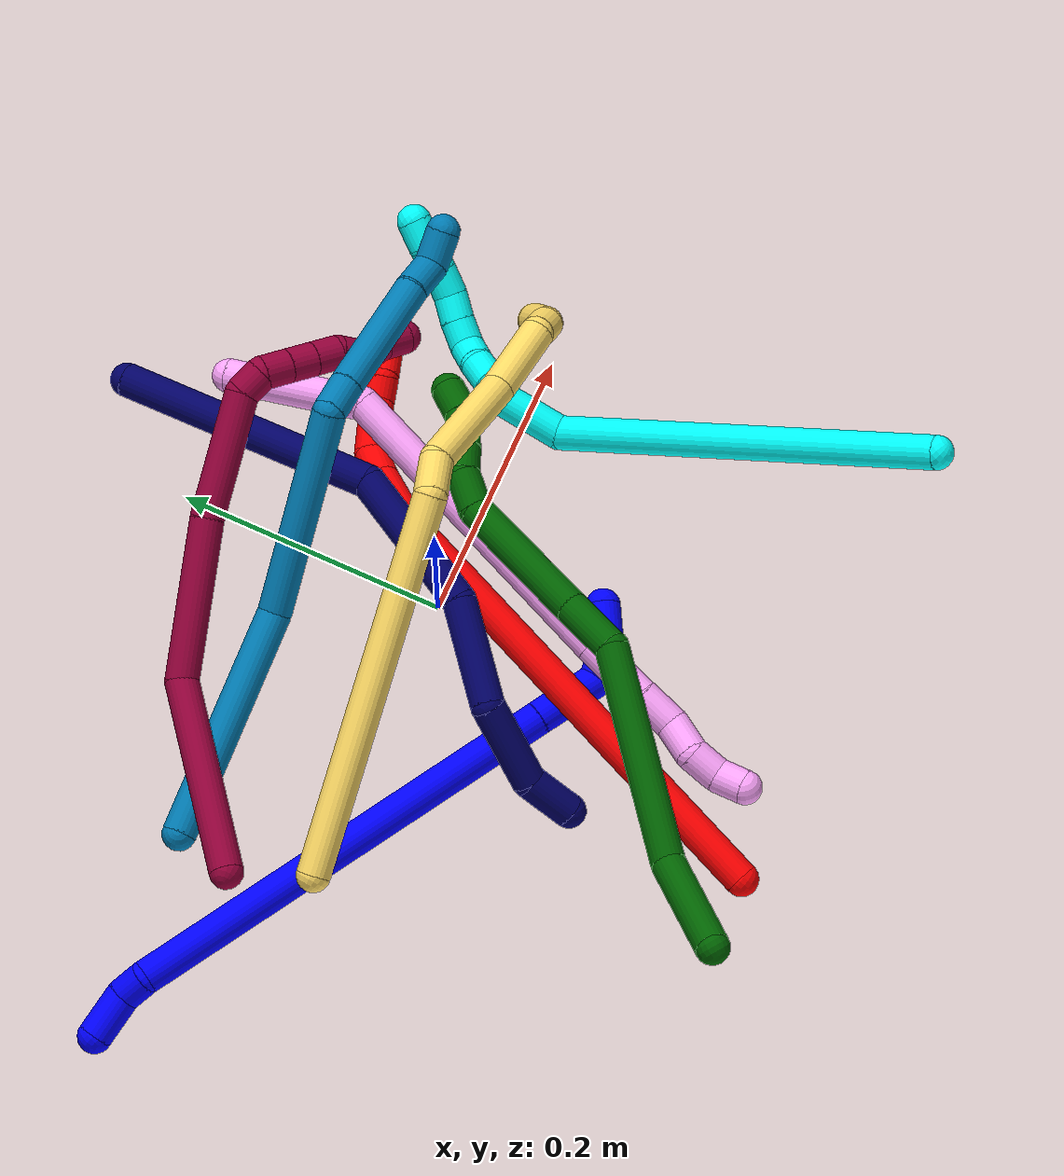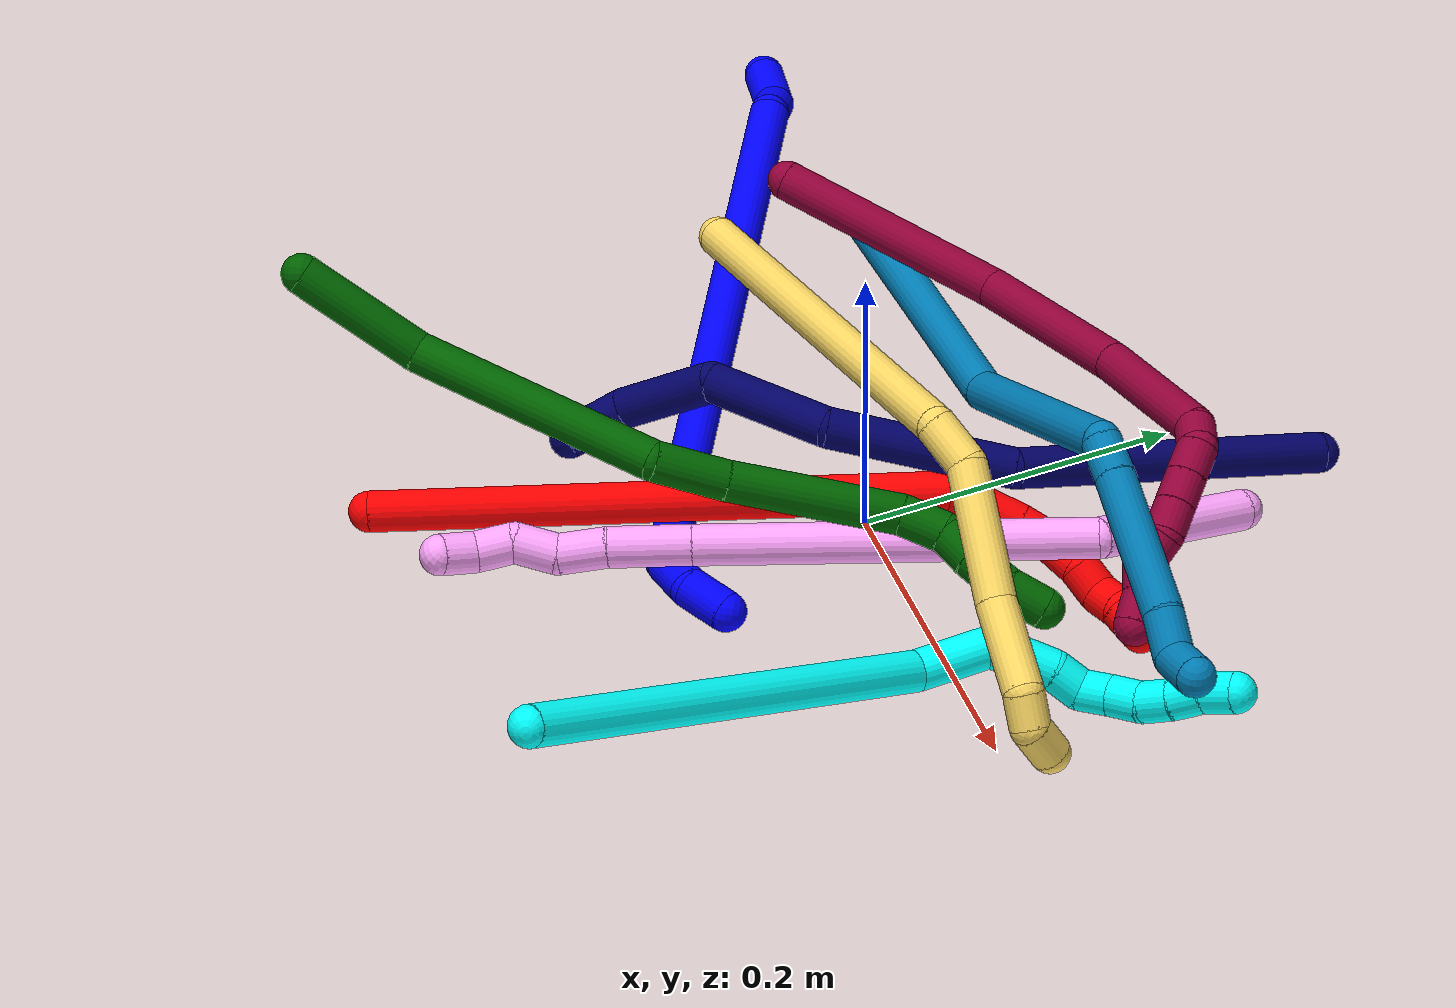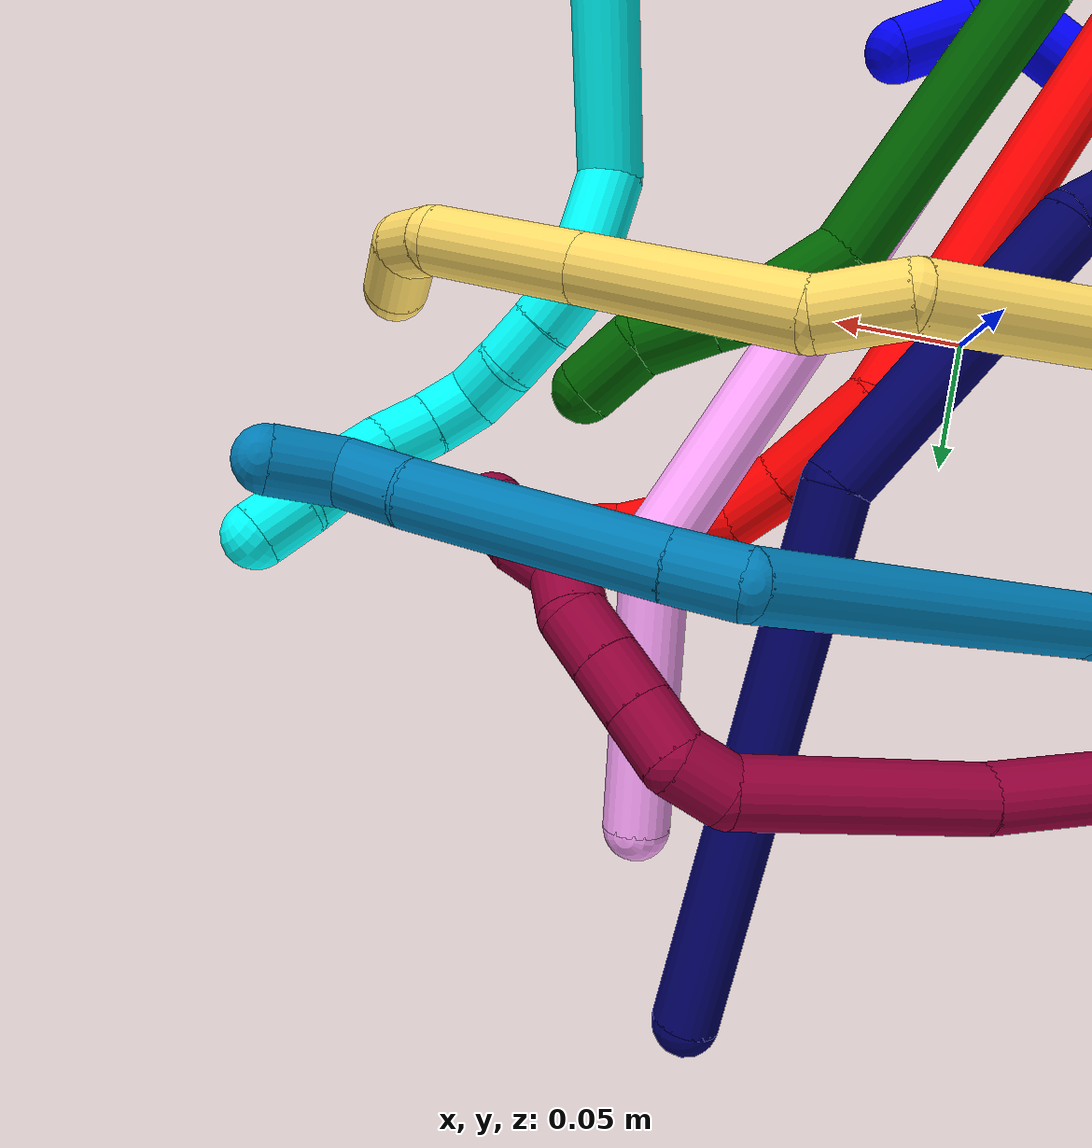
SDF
<sdf version="1.7">
 <world name="default">
  <plugin name="TubeGeneratorPlugin" filename="libtube_generator_plugin.so"/>
  <model name="photoneo_s_sensor">
   <static>1</static>
   <pose>0 0 2 1.57079 1.57079 3.14159</pose>
   <link name="link">
    <inertial><mass>0.1</mass></inertial>
    <sensor name="sensor" type="depth">
     <update_rate>30</update_rate>
     <camera>
      <horizontal_fov>1.22</horizontal_fov>
      <image><width>1920</width><height>1200</height><format>B8G8R8</format></image>
      <clip><near>0.1</near><far>4</far></clip>
      <depth_camera><output>points</output></depth_camera>
     </camera>
     <plugin name="camera_plugin" filename="libgazebo_ros_depth_camera.so">
      <baseline>0.2</baseline>
      <alwaysOn>1</alwaysOn>
      <updateRate>0.0</updateRate>
      <cameraName>camera_ir</cameraName>
      <imageTopicName>/camera/color/image_raw</imageTopicName>
      <cameraInfoTopicName>/camera/color/camera_info</cameraInfoTopicName>
      <depthImageTopicName>/camera/depth/image_raw</depthImageTopicName>
      <depthImageCameraInfoTopicName>/camera/depth/camera_info</depthImageCameraInfoTopicName>
      <pointCloudTopicName>/camera/depth/points</pointCloudTopicName>
      <frameName>fr_optical</frameName>
      <pointCloudCutoff>0.1</pointCloudCutoff>
      <pointCloudCutoffMax>2.0</pointCloudCutoffMax>
      <distortionK1>0</distortionK1>
      <distortionK2>0</distortionK2>
      <distortionK3>0</distortionK3>
      <distortionT1>0</distortionT1>
      <distortionT2>0</distortionT2>
      <CxPrime>0</CxPrime>
      <Cx>0</Cx>
      <Cy>0</Cy>
      <focalLength>0</focalLength>
      <hackBaseline>0</hackBaseline>
     </plugin>
    </sensor>
   </link>
  </model>
  <gravity>0 0 -9.8</gravity>
  <magnetic_field>6e-06 2.3e-05 -4.2e-05</magnetic_field>
  <atmosphere type="adiabatic"/>
  <physics name="default_physics" default="0" type="ode">
   <max_step_size>0.003</max_step_size>
   <real_time_factor>1</real_time_factor>
   <real_time_update_rate>1000</real_time_update_rate>
   <max_contacts>10000</max_contacts>
   <ode>
    <solver>
     <type>quick</type>
     <iters>100</iters>
     <sor>1.3</sor>
     <use_dynamic_moi_rescaling>0</use_dynamic_moi_rescaling>
    </solver>
    <constraints>
     <contact_max_correcting_vel>0</contact_max_correcting_vel>
     <contact_surface_layer>0.001</contact_surface_layer>
     <cfm>0</cfm>
     <erp>0.2</erp>
    </constraints>
   </ode>
  </physics>
  <scene><ambient>0.4 0.4 0.4 1</ambient><background>0.7 0.7 0.7 1</background><shadows>0</shadows></scene>
  <audio><device>default</device></audio>
  <spherical_coordinates>
   <surface_model>EARTH_WGS84</surface_model>
   <latitude_deg>0</latitude_deg>
   <longitude_deg>0</longitude_deg>
   <elevation>0</elevation>
   <heading_deg>0</heading_deg>
  </spherical_coordinates>
  <model name="bin">
   <static>1</static>
   <link name="bottom">
    <collision name="collision-bottom">
     <pose>0 0 -0.01 0 -0 0</pose>
     <geometry><box><size>0.8 0.6 0.02</size></box></geometry>
     <surface>
      <friction><ode><mu>100</mu><mu2>100</mu2></ode></friction>
      <contact><collide_bitmask>65535</collide_bitmask></contact>
     </surface>
    </collision>
   </link>
   <link name="west_wall">
    <collision name="collision-west_wall">
     <pose>-0.41 0 0.1 0 -0 0</pose>
     <geometry><box><size>0.02 0.6 0.2</size></box></geometry>
     <surface>
      <friction><ode><mu>100</mu><mu2>100</mu2></ode></friction>
      <contact><collide_bitmask>65535</collide_bitmask></contact>
     </surface>
    </collision>
   </link>
   <link name="east_wall">
    <collision name="collision-east_wall">
     <pose>0.41 0 0.1 0 -0 0</pose>
     <geometry><box><size>0.02 0.6 0.2</size></box></geometry>
     <surface>
      <friction><ode><mu>100</mu><mu2>100</mu2></ode></friction>
      <contact><collide_bitmask>65535</collide_bitmask></contact>
     </surface>
    </collision>
   </link>
   <link name="south_wall">
    <collision name="collision-south_wall">
     <pose>0 -0.31 0.1 0 -0 0</pose>
     <geometry><box><size>0.8 0.02 0.2</size></box></geometry>
     <surface>
      <friction><ode><mu>100</mu><mu2>100</mu2></ode></friction>
      <contact><collide_bitmask>65535</collide_bitmask></contact>
     </surface>
    </collision>
   </link>
   <link name="north_wall">
    <collision name="collision-north_wall">
     <pose>0 0.31 0.1 0 -0 0</pose>
     <geometry><box><size>0.8 0.02 0.2</size></box></geometry>
     <surface>
      <friction><ode><mu>100</mu><mu2>100</mu2></ode></friction>
      <contact><collide_bitmask>65535</collide_bitmask></contact>
     </surface>
    </collision>
   </link>
  </model>
  <model name="1">
   <static>0</static>
   <link name="1">
    <collision name="collision-cylinder-e_1_1_4">
     <pose>-0.006791 0.004312 0.011949 -0.346343 -0.490933 0.087587</pose>
     <geometry><cylinder><radius>0.0125</radius><length>0.02881</length></cylinder></geometry>
     <surface>
      <friction><ode><mu>1.16</mu><mu2>1.16</mu2><slip1>0</slip1><slip2>0</slip2></ode></friction>
      <contact><ode><kp>1e+06</kp><kd>1</kd><max_vel>0</max_vel><min_depth>0.001</min_depth></ode></contact>
     </surface>
    </collision>
    <visual name="visual-cylinder-e_1_1_4">
     <pose>-0.006791 0.004312 0.011949 -0.346343 -0.490933 0.087587</pose>
     <geometry><cylinder><radius>0.0125</radius><length>0.02881</length></cylinder></geometry>
     <material><ambient>0 0 1 1</ambient></material>
    </visual>
    <collision name="collision-cylinder-e_2_4_5">
     <pose>-0.023801 0.013118 0.031541 -0.531467 -0.856198 0.247129</pose>
     <geometry><cylinder><radius>0.0125</radius><length>0.027055</length></cylinder></geometry>
     <surface>
      <friction><ode><mu>1.16</mu><mu2>1.16</mu2><slip1>0</slip1><slip2>0</slip2></ode></friction>
      <contact><ode><kp>1e+06</kp><kd>1</kd><max_vel>0</max_vel><min_depth>0.001</min_depth></ode></contact>
     </surface>
    </collision>
    <visual name="visual-cylinder-e_2_4_5">
     <pose>-0.023801 0.013118 0.031541 -0.531467 -0.856198 0.247129</pose>
     <geometry><cylinder><radius>0.0125</radius><length>0.027055</length></cylinder></geometry>
     <material><ambient>0 0 1 1</ambient></material>
    </visual>
    <collision name="collision-cylinder-e_3_5_6">
     <pose>-0.05311 0.034346 0.037773 -1.65483 -0.849306 0.914219</pose>
     <geometry><cylinder><radius>0.0125</radius><length>0.050854</length></cylinder></geometry>
     <surface>
      <friction><ode><mu>1.16</mu><mu2>1.16</mu2><slip1>0</slip1><slip2>0</slip2></ode></friction>
      <contact><ode><kp>1e+06</kp><kd>1</kd><max_vel>0</max_vel><min_depth>0.001</min_depth></ode></contact>
     </surface>
    </collision>
    <visual name="visual-cylinder-e_3_5_6">
     <pose>-0.05311 0.034346 0.037773 -1.65483 -0.849306 0.914219</pose>
     <geometry><cylinder><radius>0.0125</radius><length>0.050854</length></cylinder></geometry>
     <material><ambient>0 0 1 1</ambient></material>
    </visual>
    <collision name="collision-cylinder-e_4_6_7">
     <pose>-0.200667 0.159422 0.026115 -1.66511 -0.867985 0.942236</pose>
     <geometry><cylinder><radius>0.0125</radius><length>0.336727</length></cylinder></geometry>
     <surface>
      <friction><ode><mu>1.16</mu><mu2>1.16</mu2><slip1>0</slip1><slip2>0</slip2></ode></friction>
      <contact><ode><kp>1e+06</kp><kd>1</kd><max_vel>0</max_vel><min_depth>0.001</min_depth></ode></contact>
     </surface>
    </collision>
    <visual name="visual-cylinder-e_4_6_7">
     <pose>-0.200667 0.159422 0.026115 -1.66511 -0.867985 0.942236</pose>
     <geometry><cylinder><radius>0.0125</radius><length>0.336727</length></cylinder></geometry>
     <material><ambient>0 0 1 1</ambient></material>
    </visual>
    <collision name="collision-cylinder-e_5_7_8">
     <pose>-0.339546 0.269917 0.014636 -2.0896 -1.33692 1.8738</pose>
     <geometry><cylinder><radius>0.0125</radius><length>0.021408</length></cylinder></geometry>
     <surface>
      <friction><ode><mu>1.16</mu><mu2>1.16</mu2><slip1>0</slip1><slip2>0</slip2></ode></friction>
      <contact><ode><kp>1e+06</kp><kd>1</kd><max_vel>0</max_vel><min_depth>0.001</min_depth></ode></contact>
     </surface>
    </collision>
    <visual name="visual-cylinder-e_5_7_8">
     <pose>-0.339546 0.269917 0.014636 -2.0896 -1.33692 1.8738</pose>
     <geometry><cylinder><radius>0.0125</radius><length>0.021408</length></cylinder></geometry>
     <material><ambient>0 0 1 1</ambient></material>
    </visual>
    <collision name="collision-cylinder-e_6_8_2">
     <pose>-0.365245 0.279529 0.017823 -1.03611 -1.05496 0.641168</pose>
     <geometry><cylinder><radius>0.0125</radius><length>0.035146</length></cylinder></geometry>
     <surface>
      <friction><ode><mu>1.16</mu><mu2>1.16</mu2><slip1>0</slip1><slip2>0</slip2></ode></friction>
      <contact><ode><kp>1e+06</kp><kd>1</kd><max_vel>0</max_vel><min_depth>0.001</min_depth></ode></contact>
     </surface>
    </collision>
    <visual name="visual-cylinder-e_6_8_2">
     <pose>-0.365245 0.279529 0.017823 -1.03611 -1.05496 0.641168</pose>
     <geometry><cylinder><radius>0.0125</radius><length>0.035146</length></cylinder></geometry>
     <material><ambient>0 0 1 1</ambient></material>
    </visual>
    <collision name="collision-sphere-2">
     <pose>-0.380531 0.286987 0.02224 0 -0 0</pose>
     <geometry><sphere><radius>0.0125</radius></sphere></geometry>
     <surface>
      <friction><ode><mu>1.16</mu><mu2>1.16</mu2><slip1>0</slip1><slip2>0</slip2></ode></friction>
      <contact><ode><kp>1e+06</kp><kd>1</kd><max_vel>0</max_vel><min_depth>0.001</min_depth></ode></contact>
     </surface>
    </collision>
    <visual name="visual-sphere-2">
     <pose>-0.380531 0.286987 0.02224 0 -0 0</pose>
     <geometry><sphere><radius>0.0125</radius></sphere></geometry>
     <material><ambient>0 0 1 1</ambient></material>
    </visual>
    <collision name="collision-sphere-4">
     <pose>-0.013582 0.008625 0.023899 0 -0 0</pose>
     <geometry><sphere><radius>0.0125</radius></sphere></geometry>
     <surface>
      <friction><ode><mu>1.16</mu><mu2>1.16</mu2><slip1>0</slip1><slip2>0</slip2></ode></friction>
      <contact><ode><kp>1e+06</kp><kd>1</kd><max_vel>0</max_vel><min_depth>0.001</min_depth></ode></contact>
     </surface>
    </collision>
    <visual name="visual-sphere-4">
     <pose>-0.013582 0.008625 0.023899 0 -0 0</pose>
     <geometry><sphere><radius>0.0125</radius></sphere></geometry>
     <material><ambient>0 0 1 1</ambient></material>
    </visual>
    <collision name="collision-sphere-1">
     <geometry><sphere><radius>0.0125</radius></sphere></geometry>
     <surface>
      <friction><ode><mu>1.16</mu><mu2>1.16</mu2><slip1>0</slip1><slip2>0</slip2></ode></friction>
      <contact><ode><kp>1e+06</kp><kd>1</kd><max_vel>0</max_vel><min_depth>0.001</min_depth></ode></contact>
     </surface>
    </collision>
    <visual name="visual-sphere-1">
     <geometry><sphere><radius>0.0125</radius></sphere></geometry>
     <material><ambient>0 0 1 1</ambient></material>
    </visual>
    <collision name="collision-sphere-8">
     <pose>-0.349958 0.272071 0.013406 0 -0 0</pose>
     <geometry><sphere><radius>0.0125</radius></sphere></geometry>
     <surface>
      <friction><ode><mu>1.16</mu><mu2>1.16</mu2><slip1>0</slip1><slip2>0</slip2></ode></friction>
      <contact><ode><kp>1e+06</kp><kd>1</kd><max_vel>0</max_vel><min_depth>0.001</min_depth></ode></contact>
     </surface>
    </collision>
    <visual name="visual-sphere-8">
     <pose>-0.349958 0.272071 0.013406 0 -0 0</pose>
     <geometry><sphere><radius>0.0125</radius></sphere></geometry>
     <material><ambient>0 0 1 1</ambient></material>
    </visual>
    <collision name="collision-sphere-5">
     <pose>-0.034019 0.01761 0.039183 0 -0 0</pose>
     <geometry><sphere><radius>0.0125</radius></sphere></geometry>
     <surface>
      <friction><ode><mu>1.16</mu><mu2>1.16</mu2><slip1>0</slip1><slip2>0</slip2></ode></friction>
      <contact><ode><kp>1e+06</kp><kd>1</kd><max_vel>0</max_vel><min_depth>0.001</min_depth></ode></contact>
     </surface>
    </collision>
    <visual name="visual-sphere-5">
     <pose>-0.034019 0.01761 0.039183 0 -0 0</pose>
     <geometry><sphere><radius>0.0125</radius></sphere></geometry>
     <material><ambient>0 0 1 1</ambient></material>
    </visual>
    <collision name="collision-sphere-6">
     <pose>-0.072201 0.051081 0.036364 0 -0 0</pose>
     <geometry><sphere><radius>0.0125</radius></sphere></geometry>
     <surface>
      <friction><ode><mu>1.16</mu><mu2>1.16</mu2><slip1>0</slip1><slip2>0</slip2></ode></friction>
      <contact><ode><kp>1e+06</kp><kd>1</kd><max_vel>0</max_vel><min_depth>0.001</min_depth></ode></contact>
     </surface>
    </collision>
    <visual name="visual-sphere-6">
     <pose>-0.072201 0.051081 0.036364 0 -0 0</pose>
     <geometry><sphere><radius>0.0125</radius></sphere></geometry>
     <material><ambient>0 0 1 1</ambient></material>
    </visual>
    <collision name="collision-sphere-7">
     <pose>-0.329133 0.267763 0.015866 0 -0 0</pose>
     <geometry><sphere><radius>0.0125</radius></sphere></geometry>
     <surface>
      <friction><ode><mu>1.16</mu><mu2>1.16</mu2><slip1>0</slip1><slip2>0</slip2></ode></friction>
      <contact><ode><kp>1e+06</kp><kd>1</kd><max_vel>0</max_vel><min_depth>0.001</min_depth></ode></contact>
     </surface>
    </collision>
    <visual name="visual-sphere-7">
     <pose>-0.329133 0.267763 0.015866 0 -0 0</pose>
     <geometry><sphere><radius>0.0125</radius></sphere></geometry>
     <material><ambient>0 0 1 1</ambient></material>
    </visual>
    <inertial>
     <pose>-0.182433 0.14302 0.025704 0 -0 0</pose>
     <mass>0.5</mass>
     <inertia>
      <ixx>0.002876</ixx>
      <ixy>0</ixy>
      <ixz>0</ixz>
      <iyy>0.003507</iyy>
      <iyz>0</iyz>
      <izz>0.00039</izz>
     </inertia>
    </inertial>
   </link>
   <pose>0.047899 -0.108608 0.012496 1.39109 -0.645417 -0.367622</pose>
  </model>
  <model name="2">
   <static>0</static>
   <link name="2">
    <collision name="collision-cylinder-e_1_1_4">
     <pose>0.015736 0.170426 0.034529 -1.3709 0.09025 -0.073815</pose>
     <geometry><cylinder><radius>0.0125</radius><length>0.349198</length></cylinder></geometry>
     <surface>
      <friction><ode><mu>1.16</mu><mu2>1.16</mu2><slip1>0</slip1><slip2>0</slip2></ode></friction>
      <contact><ode><kp>1e+06</kp><kd>1</kd><max_vel>0</max_vel><min_depth>0.001</min_depth></ode></contact>
     </surface>
    </collision>
    <visual name="visual-cylinder-e_1_1_4">
     <pose>0.015736 0.170426 0.034529 -1.3709 0.09025 -0.073815</pose>
     <geometry><cylinder><radius>0.0125</radius><length>0.349198</length></cylinder></geometry>
     <material><ambient>1 0 0 1</ambient></material>
    </visual>
    <collision name="collision-cylinder-e_2_4_5">
     <pose>0.042153 0.357975 0.07832 -1.07493 0.501784 -0.303151</pose>
     <geometry><cylinder><radius>0.0125</radius><length>0.04441</length></cylinder></geometry>
     <surface>
      <friction><ode><mu>1.16</mu><mu2>1.16</mu2><slip1>0</slip1><slip2>0</slip2></ode></friction>
      <contact><ode><kp>1e+06</kp><kd>1</kd><max_vel>0</max_vel><min_depth>0.001</min_depth></ode></contact>
     </surface>
    </collision>
    <visual name="visual-cylinder-e_2_4_5">
     <pose>0.042153 0.357975 0.07832 -1.07493 0.501784 -0.303151</pose>
     <geometry><cylinder><radius>0.0125</radius><length>0.04441</length></cylinder></geometry>
     <material><ambient>1 0 0 1</ambient></material>
    </visual>
    <collision name="collision-cylinder-e_3_5_6">
     <pose>0.058599 0.383643 0.093682 -0.950928 0.502225 -0.262631</pose>
     <geometry><cylinder><radius>0.0125</radius><length>0.023955</length></cylinder></geometry>
     <surface>
      <friction><ode><mu>1.16</mu><mu2>1.16</mu2><slip1>0</slip1><slip2>0</slip2></ode></friction>
      <contact><ode><kp>1e+06</kp><kd>1</kd><max_vel>0</max_vel><min_depth>0.001</min_depth></ode></contact>
     </surface>
    </collision>
    <visual name="visual-cylinder-e_3_5_6">
     <pose>0.058599 0.383643 0.093682 -0.950928 0.502225 -0.262631</pose>
     <geometry><cylinder><radius>0.0125</radius><length>0.023955</length></cylinder></geometry>
     <material><ambient>1 0 0 1</ambient></material>
    </visual>
    <collision name="collision-cylinder-e_4_6_7">
     <pose>0.066338 0.397583 0.109399 -0.511125 0.177107 -0.046387</pose>
     <geometry><cylinder><radius>0.0125</radius><length>0.022408</length></cylinder></geometry>
     <surface>
      <friction><ode><mu>1.16</mu><mu2>1.16</mu2><slip1>0</slip1><slip2>0</slip2></ode></friction>
      <contact><ode><kp>1e+06</kp><kd>1</kd><max_vel>0</max_vel><min_depth>0.001</min_depth></ode></contact>
     </surface>
    </collision>
    <visual name="visual-cylinder-e_4_6_7">
     <pose>0.066338 0.397583 0.109399 -0.511125 0.177107 -0.046387</pose>
     <geometry><cylinder><radius>0.0125</radius><length>0.022408</length></cylinder></geometry>
     <material><ambient>1 0 0 1</ambient></material>
    </visual>
    <collision name="collision-cylinder-e_5_7_8">
     <pose>0.073752 0.406897 0.12644 -0.485894 0.575014 -0.146312</pose>
     <geometry><cylinder><radius>0.0125</radius><length>0.020003</length></cylinder></geometry>
     <surface>
      <friction><ode><mu>1.16</mu><mu2>1.16</mu2><slip1>0</slip1><slip2>0</slip2></ode></friction>
      <contact><ode><kp>1e+06</kp><kd>1</kd><max_vel>0</max_vel><min_depth>0.001</min_depth></ode></contact>
     </surface>
    </collision>
    <visual name="visual-cylinder-e_5_7_8">
     <pose>0.073752 0.406897 0.12644 -0.485894 0.575014 -0.146312</pose>
     <geometry><cylinder><radius>0.0125</radius><length>0.020003</length></cylinder></geometry>
     <material><ambient>1 0 0 1</ambient></material>
    </visual>
    <collision name="collision-cylinder-e_6_8_9">
     <pose>0.078193 0.415206 0.142805 -0.456271 -0.099781 0.023185</pose>
     <geometry><cylinder><radius>0.0125</radius><length>0.020025</length></cylinder></geometry>
     <surface>
      <friction><ode><mu>1.16</mu><mu2>1.16</mu2><slip1>0</slip1><slip2>0</slip2></ode></friction>
      <contact><ode><kp>1e+06</kp><kd>1</kd><max_vel>0</max_vel><min_depth>0.001</min_depth></ode></contact>
     </surface>
    </collision>
    <visual name="visual-cylinder-e_6_8_9">
     <pose>0.078193 0.415206 0.142805 -0.456271 -0.099781 0.023185</pose>
     <geometry><cylinder><radius>0.0125</radius><length>0.020025</length></cylinder></geometry>
     <material><ambient>1 0 0 1</ambient></material>
    </visual>
    <collision name="collision-cylinder-e_7_9_2">
     <pose>0.080435 0.423764 0.160243 -0.456222 0.329807 -0.077229</pose>
     <geometry><cylinder><radius>0.0125</radius><length>0.020001</length></cylinder></geometry>
     <surface>
      <friction><ode><mu>1.16</mu><mu2>1.16</mu2><slip1>0</slip1><slip2>0</slip2></ode></friction>
      <contact><ode><kp>1e+06</kp><kd>1</kd><max_vel>0</max_vel><min_depth>0.001</min_depth></ode></contact>
     </surface>
    </collision>
    <visual name="visual-cylinder-e_7_9_2">
     <pose>0.080435 0.423764 0.160243 -0.456222 0.329807 -0.077229</pose>
     <geometry><cylinder><radius>0.0125</radius><length>0.020001</length></cylinder></geometry>
     <material><ambient>1 0 0 1</ambient></material>
    </visual>
    <collision name="collision-sphere-2">
     <pose>0.083674 0.427933 0.168737 0 -0 0</pose>
     <geometry><sphere><radius>0.0125</radius></sphere></geometry>
     <surface>
      <friction><ode><mu>1.16</mu><mu2>1.16</mu2><slip1>0</slip1><slip2>0</slip2></ode></friction>
      <contact><ode><kp>1e+06</kp><kd>1</kd><max_vel>0</max_vel><min_depth>0.001</min_depth></ode></contact>
     </surface>
    </collision>
    <visual name="visual-sphere-2">
     <pose>0.083674 0.427933 0.168737 0 -0 0</pose>
     <geometry><sphere><radius>0.0125</radius></sphere></geometry>
     <material><ambient>1 0 0 1</ambient></material>
    </visual>
    <collision name="collision-sphere-9">
     <pose>0.077196 0.419596 0.151749 0 -0 0</pose>
     <geometry><sphere><radius>0.0125</radius></sphere></geometry>
     <surface>
      <friction><ode><mu>1.16</mu><mu2>1.16</mu2><slip1>0</slip1><slip2>0</slip2></ode></friction>
      <contact><ode><kp>1e+06</kp><kd>1</kd><max_vel>0</max_vel><min_depth>0.001</min_depth></ode></contact>
     </surface>
    </collision>
    <visual name="visual-sphere-9">
     <pose>0.077196 0.419596 0.151749 0 -0 0</pose>
     <geometry><sphere><radius>0.0125</radius></sphere></geometry>
     <material><ambient>1 0 0 1</ambient></material>
    </visual>
    <collision name="collision-sphere-4">
     <pose>0.031472 0.340852 0.069058 0 -0 0</pose>
     <geometry><sphere><radius>0.0125</radius></sphere></geometry>
     <surface>
      <friction><ode><mu>1.16</mu><mu2>1.16</mu2><slip1>0</slip1><slip2>0</slip2></ode></friction>
      <contact><ode><kp>1e+06</kp><kd>1</kd><max_vel>0</max_vel><min_depth>0.001</min_depth></ode></contact>
     </surface>
    </collision>
    <visual name="visual-sphere-4">
     <pose>0.031472 0.340852 0.069058 0 -0 0</pose>
     <geometry><sphere><radius>0.0125</radius></sphere></geometry>
     <material><ambient>1 0 0 1</ambient></material>
    </visual>
    <collision name="collision-sphere-1">
     <geometry><sphere><radius>0.0125</radius></sphere></geometry>
     <surface>
      <friction><ode><mu>1.16</mu><mu2>1.16</mu2><slip1>0</slip1><slip2>0</slip2></ode></friction>
      <contact><ode><kp>1e+06</kp><kd>1</kd><max_vel>0</max_vel><min_depth>0.001</min_depth></ode></contact>
     </surface>
    </collision>
    <visual name="visual-sphere-1">
     <geometry><sphere><radius>0.0125</radius></sphere></geometry>
     <material><ambient>1 0 0 1</ambient></material>
    </visual>
    <collision name="collision-sphere-8">
     <pose>0.079191 0.410817 0.133862 0 -0 0</pose>
     <geometry><sphere><radius>0.0125</radius></sphere></geometry>
     <surface>
      <friction><ode><mu>1.16</mu><mu2>1.16</mu2><slip1>0</slip1><slip2>0</slip2></ode></friction>
      <contact><ode><kp>1e+06</kp><kd>1</kd><max_vel>0</max_vel><min_depth>0.001</min_depth></ode></contact>
     </surface>
    </collision>
    <visual name="visual-sphere-8">
     <pose>0.079191 0.410817 0.133862 0 -0 0</pose>
     <geometry><sphere><radius>0.0125</radius></sphere></geometry>
     <material><ambient>1 0 0 1</ambient></material>
    </visual>
    <collision name="collision-sphere-5">
     <pose>0.052833 0.375098 0.087583 0 -0 0</pose>
     <geometry><sphere><radius>0.0125</radius></sphere></geometry>
     <surface>
      <friction><ode><mu>1.16</mu><mu2>1.16</mu2><slip1>0</slip1><slip2>0</slip2></ode></friction>
      <contact><ode><kp>1e+06</kp><kd>1</kd><max_vel>0</max_vel><min_depth>0.001</min_depth></ode></contact>
     </surface>
    </collision>
    <visual name="visual-sphere-5">
     <pose>0.052833 0.375098 0.087583 0 -0 0</pose>
     <geometry><sphere><radius>0.0125</radius></sphere></geometry>
     <material><ambient>1 0 0 1</ambient></material>
    </visual>
    <collision name="collision-sphere-6">
     <pose>0.064365 0.392188 0.09978 0 -0 0</pose>
     <geometry><sphere><radius>0.0125</radius></sphere></geometry>
     <surface>
      <friction><ode><mu>1.16</mu><mu2>1.16</mu2><slip1>0</slip1><slip2>0</slip2></ode></friction>
      <contact><ode><kp>1e+06</kp><kd>1</kd><max_vel>0</max_vel><min_depth>0.001</min_depth></ode></contact>
     </surface>
    </collision>
    <visual name="visual-sphere-6">
     <pose>0.064365 0.392188 0.09978 0 -0 0</pose>
     <geometry><sphere><radius>0.0125</radius></sphere></geometry>
     <material><ambient>1 0 0 1</ambient></material>
    </visual>
    <collision name="collision-sphere-7">
     <pose>0.068312 0.402978 0.119019 0 -0 0</pose>
     <geometry><sphere><radius>0.0125</radius></sphere></geometry>
     <surface>
      <friction><ode><mu>1.16</mu><mu2>1.16</mu2><slip1>0</slip1><slip2>0</slip2></ode></friction>
      <contact><ode><kp>1e+06</kp><kd>1</kd><max_vel>0</max_vel><min_depth>0.001</min_depth></ode></contact>
     </surface>
    </collision>
    <visual name="visual-sphere-7">
     <pose>0.068312 0.402978 0.119019 0 -0 0</pose>
     <geometry><sphere><radius>0.0125</radius></sphere></geometry>
     <material><ambient>1 0 0 1</ambient></material>
    </visual>
    <inertial>
     <pose>0.029814 0.236877 0.05765 0 -0 0</pose>
     <mass>0.5</mass>
     <inertia>
      <ixx>0.003295</ixx>
      <ixy>0</ixy>
      <ixz>0</ixz>
      <iyy>0.000509</iyy>
      <iyz>0</iyz>
      <izz>-0.003803</izz>
     </inertia>
    </inertial>
   </link>
   <pose>-0.097197 -0.280732 0.026262 1.331 1.42112 1.13315</pose>
  </model>
  <model name="3">
   <static>0</static>
   <link name="3">
    <collision name="collision-cylinder-e_1_1_4">
     <pose>-0.008751 0.097196 -0.110296 -2.41924 -0.059453 0.157112</pose>
     <geometry><cylinder><radius>0.0125</radius><length>0.294542</length></cylinder></geometry>
     <surface>
      <friction><ode><mu>1.16</mu><mu2>1.16</mu2><slip1>0</slip1><slip2>0</slip2></ode></friction>
      <contact><ode><kp>1e+06</kp><kd>1</kd><max_vel>0</max_vel><min_depth>0.001</min_depth></ode></contact>
     </surface>
    </collision>
    <visual name="visual-cylinder-e_1_1_4">
     <pose>-0.008751 0.097196 -0.110296 -2.41924 -0.059453 0.157112</pose>
     <geometry><cylinder><radius>0.0125</radius><length>0.294542</length></cylinder></geometry>
     <material><ambient>0.003922 1 0.996078 1</ambient></material>
    </visual>
    <collision name="collision-cylinder-e_2_4_5">
     <pose>-0.028614 0.21272 -0.227071 -1.91063 -0.51933 0.718771</pose>
     <geometry><cylinder><radius>0.0125</radius><length>0.044785</length></cylinder></geometry>
     <surface>
      <friction><ode><mu>1.16</mu><mu2>1.16</mu2><slip1>0</slip1><slip2>0</slip2></ode></friction>
      <contact><ode><kp>1e+06</kp><kd>1</kd><max_vel>0</max_vel><min_depth>0.001</min_depth></ode></contact>
     </surface>
    </collision>
    <visual name="visual-cylinder-e_2_4_5">
     <pose>-0.028614 0.21272 -0.227071 -1.91063 -0.51933 0.718771</pose>
     <geometry><cylinder><radius>0.0125</radius><length>0.044785</length></cylinder></geometry>
     <material><ambient>0.003922 1 0.996078 1</ambient></material>
    </visual>
    <collision name="collision-cylinder-e_3_5_6">
     <pose>-0.039136 0.241161 -0.234904 -1.70377 0.057932 -0.066192</pose>
     <geometry><cylinder><radius>0.0125</radius><length>0.02044</length></cylinder></geometry>
     <surface>
      <friction><ode><mu>1.16</mu><mu2>1.16</mu2><slip1>0</slip1><slip2>0</slip2></ode></friction>
      <contact><ode><kp>1e+06</kp><kd>1</kd><max_vel>0</max_vel><min_depth>0.001</min_depth></ode></contact>
     </surface>
    </collision>
    <visual name="visual-cylinder-e_3_5_6">
     <pose>-0.039136 0.241161 -0.234904 -1.70377 0.057932 -0.066192</pose>
     <geometry><cylinder><radius>0.0125</radius><length>0.02044</length></cylinder></geometry>
     <material><ambient>0.003922 1 0.996078 1</ambient></material>
    </visual>
    <collision name="collision-cylinder-e_4_6_7">
     <pose>-0.037289 0.261255 -0.237187 -1.66377 0.124553 -0.136671</pose>
     <geometry><cylinder><radius>0.0125</radius><length>0.020204</length></cylinder></geometry>
     <surface>
      <friction><ode><mu>1.16</mu><mu2>1.16</mu2><slip1>0</slip1><slip2>0</slip2></ode></friction>
      <contact><ode><kp>1e+06</kp><kd>1</kd><max_vel>0</max_vel><min_depth>0.001</min_depth></ode></contact>
     </surface>
    </collision>
    <visual name="visual-cylinder-e_4_6_7">
     <pose>-0.037289 0.261255 -0.237187 -1.66377 0.124553 -0.136671</pose>
     <geometry><cylinder><radius>0.0125</radius><length>0.020204</length></cylinder></geometry>
     <material><ambient>0.003922 1 0.996078 1</ambient></material>
    </visual>
    <collision name="collision-cylinder-e_5_7_8">
     <pose>-0.03205 0.280345 -0.239262 -1.69573 0.409396 -0.462213</pose>
     <geometry><cylinder><radius>0.0125</radius><length>0.020017</length></cylinder></geometry>
     <surface>
      <friction><ode><mu>1.16</mu><mu2>1.16</mu2><slip1>0</slip1><slip2>0</slip2></ode></friction>
      <contact><ode><kp>1e+06</kp><kd>1</kd><max_vel>0</max_vel><min_depth>0.001</min_depth></ode></contact>
     </surface>
    </collision>
    <visual name="visual-cylinder-e_5_7_8">
     <pose>-0.03205 0.280345 -0.239262 -1.69573 0.409396 -0.462213</pose>
     <geometry><cylinder><radius>0.0125</radius><length>0.020017</length></cylinder></geometry>
     <material><ambient>0.003922 1 0.996078 1</ambient></material>
    </visual>
    <collision name="collision-cylinder-e_6_8_9">
     <pose>-0.03012 0.298784 -0.237441 -1.26311 -0.206738 0.151479</pose>
     <geometry><cylinder><radius>0.0125</radius><length>0.020005</length></cylinder></geometry>
     <surface>
      <friction><ode><mu>1.16</mu><mu2>1.16</mu2><slip1>0</slip1><slip2>0</slip2></ode></friction>
      <contact><ode><kp>1e+06</kp><kd>1</kd><max_vel>0</max_vel><min_depth>0.001</min_depth></ode></contact>
     </surface>
    </collision>
    <visual name="visual-cylinder-e_6_8_9">
     <pose>-0.03012 0.298784 -0.237441 -1.26311 -0.206738 0.151479</pose>
     <geometry><cylinder><radius>0.0125</radius><length>0.020005</length></cylinder></geometry>
     <material><ambient>0.003922 1 0.996078 1</ambient></material>
    </visual>
    <collision name="collision-cylinder-e_7_9_10">
     <pose>-0.034121 0.31711 -0.230564 -1.16055 -0.196075 0.128775</pose>
     <geometry><cylinder><radius>0.0125</radius><length>0.020003</length></cylinder></geometry>
     <surface>
      <friction><ode><mu>1.16</mu><mu2>1.16</mu2><slip1>0</slip1><slip2>0</slip2></ode></friction>
      <contact><ode><kp>1e+06</kp><kd>1</kd><max_vel>0</max_vel><min_depth>0.001</min_depth></ode></contact>
     </surface>
    </collision>
    <visual name="visual-cylinder-e_7_9_10">
     <pose>-0.034121 0.31711 -0.230564 -1.16055 -0.196075 0.128775</pose>
     <geometry><cylinder><radius>0.0125</radius><length>0.020003</length></cylinder></geometry>
     <material><ambient>0.003922 1 0.996078 1</ambient></material>
    </visual>
    <collision name="collision-cylinder-e_8_10_11">
     <pose>-0.040761 0.334299 -0.223355 -1.18825 -0.488274 0.33344</pose>
     <geometry><cylinder><radius>0.0125</radius><length>0.020001</length></cylinder></geometry>
     <surface>
      <friction><ode><mu>1.16</mu><mu2>1.16</mu2><slip1>0</slip1><slip2>0</slip2></ode></friction>
      <contact><ode><kp>1e+06</kp><kd>1</kd><max_vel>0</max_vel><min_depth>0.001</min_depth></ode></contact>
     </surface>
    </collision>
    <visual name="visual-cylinder-e_8_10_11">
     <pose>-0.040761 0.334299 -0.223355 -1.18825 -0.488274 0.33344</pose>
     <geometry><cylinder><radius>0.0125</radius><length>0.020001</length></cylinder></geometry>
     <material><ambient>0.003922 1 0.996078 1</ambient></material>
    </visual>
    <collision name="collision-cylinder-e_9_11_12">
     <pose>-0.051105 0.350271 -0.217312 -1.23146 -0.600732 0.431447</pose>
     <geometry><cylinder><radius>0.0125</radius><length>0.020001</length></cylinder></geometry>
     <surface>
      <friction><ode><mu>1.16</mu><mu2>1.16</mu2><slip1>0</slip1><slip2>0</slip2></ode></friction>
      <contact><ode><kp>1e+06</kp><kd>1</kd><max_vel>0</max_vel><min_depth>0.001</min_depth></ode></contact>
     </surface>
    </collision>
    <visual name="visual-cylinder-e_9_11_12">
     <pose>-0.051105 0.350271 -0.217312 -1.23146 -0.600732 0.431447</pose>
     <geometry><cylinder><radius>0.0125</radius><length>0.020001</length></cylinder></geometry>
     <material><ambient>0.003922 1 0.996078 1</ambient></material>
    </visual>
    <collision name="collision-cylinder-e_10_12_2">
     <pose>-0.060437 0.366908 -0.211731 -1.26102 -0.376726 0.276494</pose>
     <geometry><cylinder><radius>0.0125</radius><length>0.020003</length></cylinder></geometry>
     <surface>
      <friction><ode><mu>1.16</mu><mu2>1.16</mu2><slip1>0</slip1><slip2>0</slip2></ode></friction>
      <contact><ode><kp>1e+06</kp><kd>1</kd><max_vel>0</max_vel><min_depth>0.001</min_depth></ode></contact>
     </surface>
    </collision>
    <visual name="visual-cylinder-e_10_12_2">
     <pose>-0.060437 0.366908 -0.211731 -1.26102 -0.376726 0.276494</pose>
     <geometry><cylinder><radius>0.0125</radius><length>0.020003</length></cylinder></geometry>
     <material><ambient>0.003922 1 0.996078 1</ambient></material>
    </visual>
    <collision name="collision-sphere-2">
     <pose>-0.064116 0.375765 -0.208896 0 -0 0</pose>
     <geometry><sphere><radius>0.0125</radius></sphere></geometry>
     <surface>
      <friction><ode><mu>1.16</mu><mu2>1.16</mu2><slip1>0</slip1><slip2>0</slip2></ode></friction>
      <contact><ode><kp>1e+06</kp><kd>1</kd><max_vel>0</max_vel><min_depth>0.001</min_depth></ode></contact>
     </surface>
    </collision>
    <visual name="visual-sphere-2">
     <pose>-0.064116 0.375765 -0.208896 0 -0 0</pose>
     <geometry><sphere><radius>0.0125</radius></sphere></geometry>
     <material><ambient>0.003922 1 0.996078 1</ambient></material>
    </visual>
    <collision name="collision-sphere-12">
     <pose>-0.056758 0.35805 -0.214566 0 -0 0</pose>
     <geometry><sphere><radius>0.0125</radius></sphere></geometry>
     <surface>
      <friction><ode><mu>1.16</mu><mu2>1.16</mu2><slip1>0</slip1><slip2>0</slip2></ode></friction>
      <contact><ode><kp>1e+06</kp><kd>1</kd><max_vel>0</max_vel><min_depth>0.001</min_depth></ode></contact>
     </surface>
    </collision>
    <visual name="visual-sphere-12">
     <pose>-0.056758 0.35805 -0.214566 0 -0 0</pose>
     <geometry><sphere><radius>0.0125</radius></sphere></geometry>
     <material><ambient>0.003922 1 0.996078 1</ambient></material>
    </visual>
    <collision name="collision-sphere-11">
     <pose>-0.045452 0.342492 -0.220058 0 -0 0</pose>
     <geometry><sphere><radius>0.0125</radius></sphere></geometry>
     <surface>
      <friction><ode><mu>1.16</mu><mu2>1.16</mu2><slip1>0</slip1><slip2>0</slip2></ode></friction>
      <contact><ode><kp>1e+06</kp><kd>1</kd><max_vel>0</max_vel><min_depth>0.001</min_depth></ode></contact>
     </surface>
    </collision>
    <visual name="visual-sphere-11">
     <pose>-0.045452 0.342492 -0.220058 0 -0 0</pose>
     <geometry><sphere><radius>0.0125</radius></sphere></geometry>
     <material><ambient>0.003922 1 0.996078 1</ambient></material>
    </visual>
    <collision name="collision-sphere-10">
     <pose>-0.03607 0.326105 -0.226652 0 -0 0</pose>
     <geometry><sphere><radius>0.0125</radius></sphere></geometry>
     <surface>
      <friction><ode><mu>1.16</mu><mu2>1.16</mu2><slip1>0</slip1><slip2>0</slip2></ode></friction>
      <contact><ode><kp>1e+06</kp><kd>1</kd><max_vel>0</max_vel><min_depth>0.001</min_depth></ode></contact>
     </surface>
    </collision>
    <visual name="visual-sphere-10">
     <pose>-0.03607 0.326105 -0.226652 0 -0 0</pose>
     <geometry><sphere><radius>0.0125</radius></sphere></geometry>
     <material><ambient>0.003922 1 0.996078 1</ambient></material>
    </visual>
    <collision name="collision-sphere-9">
     <pose>-0.032173 0.308114 -0.234476 0 -0 0</pose>
     <geometry><sphere><radius>0.0125</radius></sphere></geometry>
     <surface>
      <friction><ode><mu>1.16</mu><mu2>1.16</mu2><slip1>0</slip1><slip2>0</slip2></ode></friction>
      <contact><ode><kp>1e+06</kp><kd>1</kd><max_vel>0</max_vel><min_depth>0.001</min_depth></ode></contact>
     </surface>
    </collision>
    <visual name="visual-sphere-9">
     <pose>-0.032173 0.308114 -0.234476 0 -0 0</pose>
     <geometry><sphere><radius>0.0125</radius></sphere></geometry>
     <material><ambient>0.003922 1 0.996078 1</ambient></material>
    </visual>
    <collision name="collision-sphere-4">
     <pose>-0.017501 0.194392 -0.220591 0 -0 0</pose>
     <geometry><sphere><radius>0.0125</radius></sphere></geometry>
     <surface>
      <friction><ode><mu>1.16</mu><mu2>1.16</mu2><slip1>0</slip1><slip2>0</slip2></ode></friction>
      <contact><ode><kp>1e+06</kp><kd>1</kd><max_vel>0</max_vel><min_depth>0.001</min_depth></ode></contact>
     </surface>
    </collision>
    <visual name="visual-sphere-4">
     <pose>-0.017501 0.194392 -0.220591 0 -0 0</pose>
     <geometry><sphere><radius>0.0125</radius></sphere></geometry>
     <material><ambient>0.003922 1 0.996078 1</ambient></material>
    </visual>
    <collision name="collision-sphere-1">
     <geometry><sphere><radius>0.0125</radius></sphere></geometry>
     <surface>
      <friction><ode><mu>1.16</mu><mu2>1.16</mu2><slip1>0</slip1><slip2>0</slip2></ode></friction>
      <contact><ode><kp>1e+06</kp><kd>1</kd><max_vel>0</max_vel><min_depth>0.001</min_depth></ode></contact>
     </surface>
    </collision>
    <visual name="visual-sphere-1">
     <geometry><sphere><radius>0.0125</radius></sphere></geometry>
     <material><ambient>0.003922 1 0.996078 1</ambient></material>
    </visual>
    <collision name="collision-sphere-8">
     <pose>-0.028067 0.289454 -0.240406 0 -0 0</pose>
     <geometry><sphere><radius>0.0125</radius></sphere></geometry>
     <surface>
      <friction><ode><mu>1.16</mu><mu2>1.16</mu2><slip1>0</slip1><slip2>0</slip2></ode></friction>
      <contact><ode><kp>1e+06</kp><kd>1</kd><max_vel>0</max_vel><min_depth>0.001</min_depth></ode></contact>
     </surface>
    </collision>
    <visual name="visual-sphere-8">
     <pose>-0.028067 0.289454 -0.240406 0 -0 0</pose>
     <geometry><sphere><radius>0.0125</radius></sphere></geometry>
     <material><ambient>0.003922 1 0.996078 1</ambient></material>
    </visual>
    <collision name="collision-sphere-5">
     <pose>-0.039728 0.231048 -0.233551 0 -0 0</pose>
     <geometry><sphere><radius>0.0125</radius></sphere></geometry>
     <surface>
      <friction><ode><mu>1.16</mu><mu2>1.16</mu2><slip1>0</slip1><slip2>0</slip2></ode></friction>
      <contact><ode><kp>1e+06</kp><kd>1</kd><max_vel>0</max_vel><min_depth>0.001</min_depth></ode></contact>
     </surface>
    </collision>
    <visual name="visual-sphere-5">
     <pose>-0.039728 0.231048 -0.233551 0 -0 0</pose>
     <geometry><sphere><radius>0.0125</radius></sphere></geometry>
     <material><ambient>0.003922 1 0.996078 1</ambient></material>
    </visual>
    <collision name="collision-sphere-6">
     <pose>-0.038544 0.251274 -0.236257 0 -0 0</pose>
     <geometry><sphere><radius>0.0125</radius></sphere></geometry>
     <surface>
      <friction><ode><mu>1.16</mu><mu2>1.16</mu2><slip1>0</slip1><slip2>0</slip2></ode></friction>
      <contact><ode><kp>1e+06</kp><kd>1</kd><max_vel>0</max_vel><min_depth>0.001</min_depth></ode></contact>
     </surface>
    </collision>
    <visual name="visual-sphere-6">
     <pose>-0.038544 0.251274 -0.236257 0 -0 0</pose>
     <geometry><sphere><radius>0.0125</radius></sphere></geometry>
     <material><ambient>0.003922 1 0.996078 1</ambient></material>
    </visual>
    <collision name="collision-sphere-7">
     <pose>-0.036034 0.271235 -0.238118 0 -0 0</pose>
     <geometry><sphere><radius>0.0125</radius></sphere></geometry>
     <surface>
      <friction><ode><mu>1.16</mu><mu2>1.16</mu2><slip1>0</slip1><slip2>0</slip2></ode></friction>
      <contact><ode><kp>1e+06</kp><kd>1</kd><max_vel>0</max_vel><min_depth>0.001</min_depth></ode></contact>
     </surface>
    </collision>
    <visual name="visual-sphere-7">
     <pose>-0.036034 0.271235 -0.238118 0 -0 0</pose>
     <geometry><sphere><radius>0.0125</radius></sphere></geometry>
     <material><ambient>0.003922 1 0.996078 1</ambient></material>
    </visual>
    <inertial>
     <pose>-0.02077 0.174651 -0.158899 0 -0 0</pose>
     <mass>0.5</mass>
     <inertia>
      <ixx>0.002463</ixx>
      <ixy>0</ixy>
      <ixz>0</ixz>
      <iyy>-0.0012</iyy>
      <iyz>0</iyz>
      <izz>-0.001314</izz>
     </inertia>
    </inertial>
   </link>
   <pose>0.2113 -0.288502 0.152802 -0.350095 1.03681 -0.920252</pose>
  </model>
  <model name="4">
   <static>0</static>
   <link name="4">
    <collision name="collision-cylinder-e_1_1_4">
     <pose>0.004999 -0.052545 0.001747 1.53757 0.0948 0.091705</pose>
     <geometry><cylinder><radius>0.0125</radius><length>0.105623</length></cylinder></geometry>
     <surface>
      <friction><ode><mu>1.16</mu><mu2>1.16</mu2><slip1>0</slip1><slip2>0</slip2></ode></friction>
      <contact><ode><kp>1e+06</kp><kd>1</kd><max_vel>0</max_vel><min_depth>0.001</min_depth></ode></contact>
     </surface>
    </collision>
    <visual name="visual-cylinder-e_1_1_4">
     <pose>0.004999 -0.052545 0.001747 1.53757 0.0948 0.091705</pose>
     <geometry><cylinder><radius>0.0125</radius><length>0.105623</length></cylinder></geometry>
     <material><ambient>1 0.65098 0.996078 1</ambient></material>
    </visual>
    <collision name="collision-cylinder-e_2_4_5">
     <pose>0.063433 -0.197341 0.059916 1.02188 0.458948 0.260414</pose>
     <geometry><cylinder><radius>0.0125</radius><length>0.241237</length></cylinder></geometry>
     <surface>
      <friction><ode><mu>1.16</mu><mu2>1.16</mu2><slip1>0</slip1><slip2>0</slip2></ode></friction>
      <contact><ode><kp>1e+06</kp><kd>1</kd><max_vel>0</max_vel><min_depth>0.001</min_depth></ode></contact>
     </surface>
    </collision>
    <visual name="visual-cylinder-e_2_4_5">
     <pose>0.063433 -0.197341 0.059916 1.02188 0.458948 0.260414</pose>
     <geometry><cylinder><radius>0.0125</radius><length>0.241237</length></cylinder></geometry>
     <material><ambient>1 0.65098 0.996078 1</ambient></material>
    </visual>
    <collision name="collision-cylinder-e_3_5_6">
     <pose>0.127637 -0.309462 0.127613 1.05469 0.440487 0.259287</pose>
     <geometry><cylinder><radius>0.0125</radius><length>0.050514</length></cylinder></geometry>
     <surface>
      <friction><ode><mu>1.16</mu><mu2>1.16</mu2><slip1>0</slip1><slip2>0</slip2></ode></friction>
      <contact><ode><kp>1e+06</kp><kd>1</kd><max_vel>0</max_vel><min_depth>0.001</min_depth></ode></contact>
     </surface>
    </collision>
    <visual name="visual-cylinder-e_3_5_6">
     <pose>0.127637 -0.309462 0.127613 1.05469 0.440487 0.259287</pose>
     <geometry><cylinder><radius>0.0125</radius><length>0.050514</length></cylinder></geometry>
     <material><ambient>1 0.65098 0.996078 1</ambient></material>
    </visual>
    <collision name="collision-cylinder-e_4_6_7">
     <pose>0.143401 -0.340805 0.146779 0.968272 0.344411 0.182423</pose>
     <geometry><cylinder><radius>0.0125</radius><length>0.029588</length></cylinder></geometry>
     <surface>
      <friction><ode><mu>1.16</mu><mu2>1.16</mu2><slip1>0</slip1><slip2>0</slip2></ode></friction>
      <contact><ode><kp>1e+06</kp><kd>1</kd><max_vel>0</max_vel><min_depth>0.001</min_depth></ode></contact>
     </surface>
    </collision>
    <visual name="visual-cylinder-e_4_6_7">
     <pose>0.143401 -0.340805 0.146779 0.968272 0.344411 0.182423</pose>
     <geometry><cylinder><radius>0.0125</radius><length>0.029588</length></cylinder></geometry>
     <material><ambient>1 0.65098 0.996078 1</ambient></material>
    </visual>
    <collision name="collision-cylinder-e_5_7_8">
     <pose>0.157226 -0.361319 0.158876 1.13544 0.724805 0.474501</pose>
     <geometry><cylinder><radius>0.0125</radius><length>0.026639</length></cylinder></geometry>
     <surface>
      <friction><ode><mu>1.16</mu><mu2>1.16</mu2><slip1>0</slip1><slip2>0</slip2></ode></friction>
      <contact><ode><kp>1e+06</kp><kd>1</kd><max_vel>0</max_vel><min_depth>0.001</min_depth></ode></contact>
     </surface>
    </collision>
    <visual name="visual-cylinder-e_5_7_8">
     <pose>0.157226 -0.361319 0.158876 1.13544 0.724805 0.474501</pose>
     <geometry><cylinder><radius>0.0125</radius><length>0.026639</length></cylinder></geometry>
     <material><ambient>1 0.65098 0.996078 1</ambient></material>
    </visual>
    <collision name="collision-cylinder-e_6_8_9">
     <pose>0.169076 -0.37977 0.169959 0.939589 0.253424 0.129179</pose>
     <geometry><cylinder><radius>0.0125</radius><length>0.02408</length></cylinder></geometry>
     <surface>
      <friction><ode><mu>1.16</mu><mu2>1.16</mu2><slip1>0</slip1><slip2>0</slip2></ode></friction>
      <contact><ode><kp>1e+06</kp><kd>1</kd><max_vel>0</max_vel><min_depth>0.001</min_depth></ode></contact>
     </surface>
    </collision>
    <visual name="visual-cylinder-e_6_8_9">
     <pose>0.169076 -0.37977 0.169959 0.939589 0.253424 0.129179</pose>
     <geometry><cylinder><radius>0.0125</radius><length>0.02408</length></cylinder></geometry>
     <material><ambient>1 0.65098 0.996078 1</ambient></material>
    </visual>
    <collision name="collision-cylinder-e_7_9_2">
     <pose>0.174836 -0.39989 0.178352 1.43025 0.248264 0.215883</pose>
     <geometry><cylinder><radius>0.0125</radius><length>0.022319</length></cylinder></geometry>
     <surface>
      <friction><ode><mu>1.16</mu><mu2>1.16</mu2><slip1>0</slip1><slip2>0</slip2></ode></friction>
      <contact><ode><kp>1e+06</kp><kd>1</kd><max_vel>0</max_vel><min_depth>0.001</min_depth></ode></contact>
     </surface>
    </collision>
    <visual name="visual-cylinder-e_7_9_2">
     <pose>0.174836 -0.39989 0.178352 1.43025 0.248264 0.215883</pose>
     <geometry><cylinder><radius>0.0125</radius><length>0.022319</length></cylinder></geometry>
     <material><ambient>1 0.65098 0.996078 1</ambient></material>
    </visual>
    <collision name="collision-sphere-2">
     <pose>0.177579 -0.410601 0.179868 0 -0 0</pose>
     <geometry><sphere><radius>0.0125</radius></sphere></geometry>
     <surface>
      <friction><ode><mu>1.16</mu><mu2>1.16</mu2><slip1>0</slip1><slip2>0</slip2></ode></friction>
      <contact><ode><kp>1e+06</kp><kd>1</kd><max_vel>0</max_vel><min_depth>0.001</min_depth></ode></contact>
     </surface>
    </collision>
    <visual name="visual-sphere-2">
     <pose>0.177579 -0.410601 0.179868 0 -0 0</pose>
     <geometry><sphere><radius>0.0125</radius></sphere></geometry>
     <material><ambient>1 0.65098 0.996078 1</ambient></material>
    </visual>
    <collision name="collision-sphere-9">
     <pose>0.172094 -0.389179 0.176837 0 -0 0</pose>
     <geometry><sphere><radius>0.0125</radius></sphere></geometry>
     <surface>
      <friction><ode><mu>1.16</mu><mu2>1.16</mu2><slip1>0</slip1><slip2>0</slip2></ode></friction>
      <contact><ode><kp>1e+06</kp><kd>1</kd><max_vel>0</max_vel><min_depth>0.001</min_depth></ode></contact>
     </surface>
    </collision>
    <visual name="visual-sphere-9">
     <pose>0.172094 -0.389179 0.176837 0 -0 0</pose>
     <geometry><sphere><radius>0.0125</radius></sphere></geometry>
     <material><ambient>1 0.65098 0.996078 1</ambient></material>
    </visual>
    <collision name="collision-sphere-4">
     <pose>0.009998 -0.10509 0.003494 0 -0 0</pose>
     <geometry><sphere><radius>0.0125</radius></sphere></geometry>
     <surface>
      <friction><ode><mu>1.16</mu><mu2>1.16</mu2><slip1>0</slip1><slip2>0</slip2></ode></friction>
      <contact><ode><kp>1e+06</kp><kd>1</kd><max_vel>0</max_vel><min_depth>0.001</min_depth></ode></contact>
     </surface>
    </collision>
    <visual name="visual-sphere-4">
     <pose>0.009998 -0.10509 0.003494 0 -0 0</pose>
     <geometry><sphere><radius>0.0125</radius></sphere></geometry>
     <material><ambient>1 0.65098 0.996078 1</ambient></material>
    </visual>
    <collision name="collision-sphere-1">
     <geometry><sphere><radius>0.0125</radius></sphere></geometry>
     <surface>
      <friction><ode><mu>1.16</mu><mu2>1.16</mu2><slip1>0</slip1><slip2>0</slip2></ode></friction>
      <contact><ode><kp>1e+06</kp><kd>1</kd><max_vel>0</max_vel><min_depth>0.001</min_depth></ode></contact>
     </surface>
    </collision>
    <visual name="visual-sphere-1">
     <geometry><sphere><radius>0.0125</radius></sphere></geometry>
     <material><ambient>1 0.65098 0.996078 1</ambient></material>
    </visual>
    <collision name="collision-sphere-8">
     <pose>0.166057 -0.37036 0.163081 0 -0 0</pose>
     <geometry><sphere><radius>0.0125</radius></sphere></geometry>
     <surface>
      <friction><ode><mu>1.16</mu><mu2>1.16</mu2><slip1>0</slip1><slip2>0</slip2></ode></friction>
      <contact><ode><kp>1e+06</kp><kd>1</kd><max_vel>0</max_vel><min_depth>0.001</min_depth></ode></contact>
     </surface>
    </collision>
    <visual name="visual-sphere-8">
     <pose>0.166057 -0.37036 0.163081 0 -0 0</pose>
     <geometry><sphere><radius>0.0125</radius></sphere></geometry>
     <material><ambient>1 0.65098 0.996078 1</ambient></material>
    </visual>
    <collision name="collision-sphere-5">
     <pose>0.116867 -0.289591 0.116338 0 -0 0</pose>
     <geometry><sphere><radius>0.0125</radius></sphere></geometry>
     <surface>
      <friction><ode><mu>1.16</mu><mu2>1.16</mu2><slip1>0</slip1><slip2>0</slip2></ode></friction>
      <contact><ode><kp>1e+06</kp><kd>1</kd><max_vel>0</max_vel><min_depth>0.001</min_depth></ode></contact>
     </surface>
    </collision>
    <visual name="visual-sphere-5">
     <pose>0.116867 -0.289591 0.116338 0 -0 0</pose>
     <geometry><sphere><radius>0.0125</radius></sphere></geometry>
     <material><ambient>1 0.65098 0.996078 1</ambient></material>
    </visual>
    <collision name="collision-sphere-6">
     <pose>0.138406 -0.329332 0.138887 0 -0 0</pose>
     <geometry><sphere><radius>0.0125</radius></sphere></geometry>
     <surface>
      <friction><ode><mu>1.16</mu><mu2>1.16</mu2><slip1>0</slip1><slip2>0</slip2></ode></friction>
      <contact><ode><kp>1e+06</kp><kd>1</kd><max_vel>0</max_vel><min_depth>0.001</min_depth></ode></contact>
     </surface>
    </collision>
    <visual name="visual-sphere-6">
     <pose>0.138406 -0.329332 0.138887 0 -0 0</pose>
     <geometry><sphere><radius>0.0125</radius></sphere></geometry>
     <material><ambient>1 0.65098 0.996078 1</ambient></material>
    </visual>
    <collision name="collision-sphere-7">
     <pose>0.148396 -0.352278 0.15467 0 -0 0</pose>
     <geometry><sphere><radius>0.0125</radius></sphere></geometry>
     <surface>
      <friction><ode><mu>1.16</mu><mu2>1.16</mu2><slip1>0</slip1><slip2>0</slip2></ode></friction>
      <contact><ode><kp>1e+06</kp><kd>1</kd><max_vel>0</max_vel><min_depth>0.001</min_depth></ode></contact>
     </surface>
    </collision>
    <visual name="visual-sphere-7">
     <pose>0.148396 -0.352278 0.15467 0 -0 0</pose>
     <geometry><sphere><radius>0.0125</radius></sphere></geometry>
     <material><ambient>1 0.65098 0.996078 1</ambient></material>
    </visual>
    <inertial>
     <pose>0.077365 -0.213134 0.075466 0 -0 0</pose>
     <mass>0.5</mass>
     <inertia>
      <ixx>0.001443</ixx>
      <ixy>0</ixy>
      <ixz>0</ixz>
      <iyy>0.000981</iyy>
      <iyz>0</iyz>
      <izz>0.000494</izz>
     </inertia>
    </inertial>
   </link>
   <pose>0.091581 0.207448 0.017651 -2.85347 -0.408196 -3.01866</pose>
  </model>
  <model name="5">
   <static>0</static>
   <link name="5">
    <collision name="collision-cylinder-e_1_1_4">
     <pose>0.02386 0.016144 0.136829 -0.117444 0.171479 -0.010106</pose>
     <geometry><cylinder><radius>0.0125</radius><length>0.279658</length></cylinder></geometry>
     <surface>
      <friction><ode><mu>1.16</mu><mu2>1.16</mu2><slip1>0</slip1><slip2>0</slip2></ode></friction>
      <contact><ode><kp>1e+06</kp><kd>1</kd><max_vel>0</max_vel><min_depth>0.001</min_depth></ode></contact>
     </surface>
    </collision>
    <visual name="visual-cylinder-e_1_1_4">
     <pose>0.02386 0.016144 0.136829 -0.117444 0.171479 -0.010106</pose>
     <geometry><cylinder><radius>0.0125</radius><length>0.279658</length></cylinder></geometry>
     <material><ambient>1 0.858824 0.4 1</ambient></material>
    </visual>
    <collision name="collision-cylinder-e_2_4_5">
     <pose>0.054915 0.026688 0.28618 0.420558 0.483008 0.105046</pose>
     <geometry><cylinder><radius>0.0125</radius><length>0.03098</length></cylinder></geometry>
     <surface>
      <friction><ode><mu>1.16</mu><mu2>1.16</mu2><slip1>0</slip1><slip2>0</slip2></ode></friction>
      <contact><ode><kp>1e+06</kp><kd>1</kd><max_vel>0</max_vel><min_depth>0.001</min_depth></ode></contact>
     </surface>
    </collision>
    <visual name="visual-cylinder-e_2_4_5">
     <pose>0.054915 0.026688 0.28618 0.420558 0.483008 0.105046</pose>
     <geometry><cylinder><radius>0.0125</radius><length>0.03098</length></cylinder></geometry>
     <material><ambient>1 0.858824 0.4 1</ambient></material>
    </visual>
    <collision name="collision-cylinder-e_3_5_6">
     <pose>0.066588 -0.005251 0.332342 0.664266 0.104445 0.036053</pose>
     <geometry><cylinder><radius>0.0125</radius><length>0.085916</length></cylinder></geometry>
     <surface>
      <friction><ode><mu>1.16</mu><mu2>1.16</mu2><slip1>0</slip1><slip2>0</slip2></ode></friction>
      <contact><ode><kp>1e+06</kp><kd>1</kd><max_vel>0</max_vel><min_depth>0.001</min_depth></ode></contact>
     </surface>
    </collision>
    <visual name="visual-cylinder-e_3_5_6">
     <pose>0.066588 -0.005251 0.332342 0.664266 0.104445 0.036053</pose>
     <geometry><cylinder><radius>0.0125</radius><length>0.085916</length></cylinder></geometry>
     <material><ambient>1 0.858824 0.4 1</ambient></material>
    </visual>
    <collision name="collision-cylinder-e_4_6_7">
     <pose>0.074585 -0.045836 0.391056 0.516699 0.121412 0.03212</pose>
     <geometry><cylinder><radius>0.0125</radius><length>0.058105</length></cylinder></geometry>
     <surface>
      <friction><ode><mu>1.16</mu><mu2>1.16</mu2><slip1>0</slip1><slip2>0</slip2></ode></friction>
      <contact><ode><kp>1e+06</kp><kd>1</kd><max_vel>0</max_vel><min_depth>0.001</min_depth></ode></contact>
     </surface>
    </collision>
    <visual name="visual-cylinder-e_4_6_7">
     <pose>0.074585 -0.045836 0.391056 0.516699 0.121412 0.03212</pose>
     <geometry><cylinder><radius>0.0125</radius><length>0.058105</length></cylinder></geometry>
     <material><ambient>1 0.858824 0.4 1</ambient></material>
    </visual>
    <collision name="collision-cylinder-e_5_7_8">
     <pose>0.080757 -0.068933 0.421131 1.05641 0.25531 0.149511</pose>
     <geometry><cylinder><radius>0.0125</radius><length>0.021012</length></cylinder></geometry>
     <surface>
      <friction><ode><mu>1.16</mu><mu2>1.16</mu2><slip1>0</slip1><slip2>0</slip2></ode></friction>
      <contact><ode><kp>1e+06</kp><kd>1</kd><max_vel>0</max_vel><min_depth>0.001</min_depth></ode></contact>
     </surface>
    </collision>
    <visual name="visual-cylinder-e_5_7_8">
     <pose>0.080757 -0.068933 0.421131 1.05641 0.25531 0.149511</pose>
     <geometry><cylinder><radius>0.0125</radius><length>0.021012</length></cylinder></geometry>
     <material><ambient>1 0.858824 0.4 1</ambient></material>
    </visual>
    <collision name="collision-cylinder-e_6_8_2">
     <pose>0.091893 -0.086497 0.425834 1.60495 0.771643 0.795757</pose>
     <geometry><cylinder><radius>0.0125</radius><length>0.02433</length></cylinder></geometry>
     <surface>
      <friction><ode><mu>1.16</mu><mu2>1.16</mu2><slip1>0</slip1><slip2>0</slip2></ode></friction>
      <contact><ode><kp>1e+06</kp><kd>1</kd><max_vel>0</max_vel><min_depth>0.001</min_depth></ode></contact>
     </surface>
    </collision>
    <visual name="visual-cylinder-e_6_8_2">
     <pose>0.091893 -0.086497 0.425834 1.60495 0.771643 0.795757</pose>
     <geometry><cylinder><radius>0.0125</radius><length>0.02433</length></cylinder></geometry>
     <material><ambient>1 0.858824 0.4 1</ambient></material>
    </visual>
    <collision name="collision-sphere-2">
     <pose>0.100376 -0.095212 0.425537 0 -0 0</pose>
     <geometry><sphere><radius>0.0125</radius></sphere></geometry>
     <surface>
      <friction><ode><mu>1.16</mu><mu2>1.16</mu2><slip1>0</slip1><slip2>0</slip2></ode></friction>
      <contact><ode><kp>1e+06</kp><kd>1</kd><max_vel>0</max_vel><min_depth>0.001</min_depth></ode></contact>
     </surface>
    </collision>
    <visual name="visual-sphere-2">
     <pose>0.100376 -0.095212 0.425537 0 -0 0</pose>
     <geometry><sphere><radius>0.0125</radius></sphere></geometry>
     <material><ambient>1 0.858824 0.4 1</ambient></material>
    </visual>
    <collision name="collision-sphere-4">
     <pose>0.047721 0.032288 0.273658 0 -0 0</pose>
     <geometry><sphere><radius>0.0125</radius></sphere></geometry>
     <surface>
      <friction><ode><mu>1.16</mu><mu2>1.16</mu2><slip1>0</slip1><slip2>0</slip2></ode></friction>
      <contact><ode><kp>1e+06</kp><kd>1</kd><max_vel>0</max_vel><min_depth>0.001</min_depth></ode></contact>
     </surface>
    </collision>
    <visual name="visual-sphere-4">
     <pose>0.047721 0.032288 0.273658 0 -0 0</pose>
     <geometry><sphere><radius>0.0125</radius></sphere></geometry>
     <material><ambient>1 0.858824 0.4 1</ambient></material>
    </visual>
    <collision name="collision-sphere-1">
     <geometry><sphere><radius>0.0125</radius></sphere></geometry>
     <surface>
      <friction><ode><mu>1.16</mu><mu2>1.16</mu2><slip1>0</slip1><slip2>0</slip2></ode></friction>
      <contact><ode><kp>1e+06</kp><kd>1</kd><max_vel>0</max_vel><min_depth>0.001</min_depth></ode></contact>
     </surface>
    </collision>
    <visual name="visual-sphere-1">
     <geometry><sphere><radius>0.0125</radius></sphere></geometry>
     <material><ambient>1 0.858824 0.4 1</ambient></material>
    </visual>
    <collision name="collision-sphere-8">
     <pose>0.08341 -0.077783 0.426132 0 -0 0</pose>
     <geometry><sphere><radius>0.0125</radius></sphere></geometry>
     <surface>
      <friction><ode><mu>1.16</mu><mu2>1.16</mu2><slip1>0</slip1><slip2>0</slip2></ode></friction>
      <contact><ode><kp>1e+06</kp><kd>1</kd><max_vel>0</max_vel><min_depth>0.001</min_depth></ode></contact>
     </surface>
    </collision>
    <visual name="visual-sphere-8">
     <pose>0.08341 -0.077783 0.426132 0 -0 0</pose>
     <geometry><sphere><radius>0.0125</radius></sphere></geometry>
     <material><ambient>1 0.858824 0.4 1</ambient></material>
    </visual>
    <collision name="collision-sphere-5">
     <pose>0.062109 0.021087 0.298703 0 -0 0</pose>
     <geometry><sphere><radius>0.0125</radius></sphere></geometry>
     <surface>
      <friction><ode><mu>1.16</mu><mu2>1.16</mu2><slip1>0</slip1><slip2>0</slip2></ode></friction>
      <contact><ode><kp>1e+06</kp><kd>1</kd><max_vel>0</max_vel><min_depth>0.001</min_depth></ode></contact>
     </surface>
    </collision>
    <visual name="visual-sphere-5">
     <pose>0.062109 0.021087 0.298703 0 -0 0</pose>
     <geometry><sphere><radius>0.0125</radius></sphere></geometry>
     <material><ambient>1 0.858824 0.4 1</ambient></material>
    </visual>
    <collision name="collision-sphere-6">
     <pose>0.071066 -0.03159 0.365982 0 -0 0</pose>
     <geometry><sphere><radius>0.0125</radius></sphere></geometry>
     <surface>
      <friction><ode><mu>1.16</mu><mu2>1.16</mu2><slip1>0</slip1><slip2>0</slip2></ode></friction>
      <contact><ode><kp>1e+06</kp><kd>1</kd><max_vel>0</max_vel><min_depth>0.001</min_depth></ode></contact>
     </surface>
    </collision>
    <visual name="visual-sphere-6">
     <pose>0.071066 -0.03159 0.365982 0 -0 0</pose>
     <geometry><sphere><radius>0.0125</radius></sphere></geometry>
     <material><ambient>1 0.858824 0.4 1</ambient></material>
    </visual>
    <collision name="collision-sphere-7">
     <pose>0.078104 -0.060083 0.41613 0 -0 0</pose>
     <geometry><sphere><radius>0.0125</radius></sphere></geometry>
     <surface>
      <friction><ode><mu>1.16</mu><mu2>1.16</mu2><slip1>0</slip1><slip2>0</slip2></ode></friction>
      <contact><ode><kp>1e+06</kp><kd>1</kd><max_vel>0</max_vel><min_depth>0.001</min_depth></ode></contact>
     </surface>
    </collision>
    <visual name="visual-sphere-7">
     <pose>0.078104 -0.060083 0.41613 0 -0 0</pose>
     <geometry><sphere><radius>0.0125</radius></sphere></geometry>
     <material><ambient>1 0.858824 0.4 1</ambient></material>
    </visual>
    <inertial>
     <pose>0.044723 -0.002652 0.235232 0 -0 0</pose>
     <mass>0.5</mass>
     <inertia>
      <ixx>0.001881</ixx>
      <ixy>0</ixy>
      <ixz>0</ixz>
      <iyy>0.001866</iyy>
      <iyz>0</iyz>
      <izz>-0.000455</izz>
     </inertia>
    </inertial>
   </link>
   <pose>-0.222734 -0.005731 0.045037 1.36444 0.28035 1.42372</pose>
  </model>
  <model name="6">
   <static>0</static>
   <link name="6">
    <collision name="collision-cylinder-e_1_1_4">
     <pose>0.013799 0.021959 -0.032404 -2.54602 0.33893 -1.01718</pose>
     <geometry><cylinder><radius>0.0125</radius><length>0.083008</length></cylinder></geometry>
     <surface>
      <friction><ode><mu>1.16</mu><mu2>1.16</mu2><slip1>0</slip1><slip2>0</slip2></ode></friction>
      <contact><ode><kp>1e+06</kp><kd>1</kd><max_vel>0</max_vel><min_depth>0.001</min_depth></ode></contact>
     </surface>
    </collision>
    <visual name="visual-cylinder-e_1_1_4">
     <pose>0.013799 0.021959 -0.032404 -2.54602 0.33893 -1.01718</pose>
     <geometry><cylinder><radius>0.0125</radius><length>0.083008</length></cylinder></geometry>
     <material><ambient>0 0.392157 0.003922 1</ambient></material>
    </visual>
    <collision name="collision-cylinder-e_2_4_5">
     <pose>0.022334 0.072241 -0.140682 -2.78431 -0.064916 0.355844</pose>
     <geometry><cylinder><radius>0.0125</radius><length>0.162319</length></cylinder></geometry>
     <surface>
      <friction><ode><mu>1.16</mu><mu2>1.16</mu2><slip1>0</slip1><slip2>0</slip2></ode></friction>
      <contact><ode><kp>1e+06</kp><kd>1</kd><max_vel>0</max_vel><min_depth>0.001</min_depth></ode></contact>
     </surface>
    </collision>
    <visual name="visual-cylinder-e_2_4_5">
     <pose>0.022334 0.072241 -0.140682 -2.78431 -0.064916 0.355844</pose>
     <geometry><cylinder><radius>0.0125</radius><length>0.162319</length></cylinder></geometry>
     <material><ambient>0 0.392157 0.003922 1</ambient></material>
    </visual>
    <collision name="collision-cylinder-e_3_5_6">
     <pose>0.027068 0.105782 -0.236202 -2.882 0.457176 -2.11903</pose>
     <geometry><cylinder><radius>0.0125</radius><length>0.045307</length></cylinder></geometry>
     <surface>
      <friction><ode><mu>1.16</mu><mu2>1.16</mu2><slip1>0</slip1><slip2>0</slip2></ode></friction>
      <contact><ode><kp>1e+06</kp><kd>1</kd><max_vel>0</max_vel><min_depth>0.001</min_depth></ode></contact>
     </surface>
    </collision>
    <visual name="visual-cylinder-e_3_5_6">
     <pose>0.027068 0.105782 -0.236202 -2.882 0.457176 -2.11903</pose>
     <geometry><cylinder><radius>0.0125</radius><length>0.045307</length></cylinder></geometry>
     <material><ambient>0 0.392157 0.003922 1</ambient></material>
    </visual>
    <collision name="collision-cylinder-e_4_6_7">
     <pose>0.057813 0.119446 -0.303857 -2.96744 0.402358 -2.33266</pose>
     <geometry><cylinder><radius>0.0125</radius><length>0.105954</length></cylinder></geometry>
     <surface>
      <friction><ode><mu>1.16</mu><mu2>1.16</mu2><slip1>0</slip1><slip2>0</slip2></ode></friction>
      <contact><ode><kp>1e+06</kp><kd>1</kd><max_vel>0</max_vel><min_depth>0.001</min_depth></ode></contact>
     </surface>
    </collision>
    <visual name="visual-cylinder-e_4_6_7">
     <pose>0.057813 0.119446 -0.303857 -2.96744 0.402358 -2.33266</pose>
     <geometry><cylinder><radius>0.0125</radius><length>0.105954</length></cylinder></geometry>
     <material><ambient>0 0.392157 0.003922 1</ambient></material>
    </visual>
    <collision name="collision-cylinder-e_5_7_8">
     <pose>0.078919 0.132599 -0.365507 -2.8094 0.024961 -0.148634</pose>
     <geometry><cylinder><radius>0.0125</radius><length>0.02887</length></cylinder></geometry>
     <surface>
      <friction><ode><mu>1.16</mu><mu2>1.16</mu2><slip1>0</slip1><slip2>0</slip2></ode></friction>
      <contact><ode><kp>1e+06</kp><kd>1</kd><max_vel>0</max_vel><min_depth>0.001</min_depth></ode></contact>
     </surface>
    </collision>
    <visual name="visual-cylinder-e_5_7_8">
     <pose>0.078919 0.132599 -0.365507 -2.8094 0.024961 -0.148634</pose>
     <geometry><cylinder><radius>0.0125</radius><length>0.02887</length></cylinder></geometry>
     <material><ambient>0 0.392157 0.003922 1</ambient></material>
    </visual>
    <collision name="collision-cylinder-e_6_8_9">
     <pose>0.078168 0.144187 -0.387302 -2.44059 -0.103734 0.282106</pose>
     <geometry><cylinder><radius>0.0125</radius><length>0.021455</length></cylinder></geometry>
     <surface>
      <friction><ode><mu>1.16</mu><mu2>1.16</mu2><slip1>0</slip1><slip2>0</slip2></ode></friction>
      <contact><ode><kp>1e+06</kp><kd>1</kd><max_vel>0</max_vel><min_depth>0.001</min_depth></ode></contact>
     </surface>
    </collision>
    <visual name="visual-cylinder-e_6_8_9">
     <pose>0.078168 0.144187 -0.387302 -2.44059 -0.103734 0.282106</pose>
     <geometry><cylinder><radius>0.0125</radius><length>0.021455</length></cylinder></geometry>
     <material><ambient>0 0.392157 0.003922 1</ambient></material>
    </visual>
    <collision name="collision-cylinder-e_7_9_10">
     <pose>0.075822 0.158924 -0.406751 -2.5339 -0.089562 0.283903</pose>
     <geometry><cylinder><radius>0.0125</radius><length>0.027626</length></cylinder></geometry>
     <surface>
      <friction><ode><mu>1.16</mu><mu2>1.16</mu2><slip1>0</slip1><slip2>0</slip2></ode></friction>
      <contact><ode><kp>1e+06</kp><kd>1</kd><max_vel>0</max_vel><min_depth>0.001</min_depth></ode></contact>
     </surface>
    </collision>
    <visual name="visual-cylinder-e_7_9_10">
     <pose>0.075822 0.158924 -0.406751 -2.5339 -0.089562 0.283903</pose>
     <geometry><cylinder><radius>0.0125</radius><length>0.027626</length></cylinder></geometry>
     <material><ambient>0 0.392157 0.003922 1</ambient></material>
    </visual>
    <collision name="collision-cylinder-e_8_10_2">
     <pose>0.078195 0.172555 -0.428801 -2.64879 0.287406 -1.04416</pose>
     <geometry><cylinder><radius>0.0125</radius><length>0.025461</length></cylinder></geometry>
     <surface>
      <friction><ode><mu>1.16</mu><mu2>1.16</mu2><slip1>0</slip1><slip2>0</slip2></ode></friction>
      <contact><ode><kp>1e+06</kp><kd>1</kd><max_vel>0</max_vel><min_depth>0.001</min_depth></ode></contact>
     </surface>
    </collision>
    <visual name="visual-cylinder-e_8_10_2">
     <pose>0.078195 0.172555 -0.428801 -2.64879 0.287406 -1.04416</pose>
     <geometry><cylinder><radius>0.0125</radius><length>0.025461</length></cylinder></geometry>
     <material><ambient>0 0.392157 0.003922 1</ambient></material>
    </visual>
    <collision name="collision-sphere-2">
     <pose>0.081804 0.178331 -0.439557 0 -0 0</pose>
     <geometry><sphere><radius>0.0125</radius></sphere></geometry>
     <surface>
      <friction><ode><mu>1.16</mu><mu2>1.16</mu2><slip1>0</slip1><slip2>0</slip2></ode></friction>
      <contact><ode><kp>1e+06</kp><kd>1</kd><max_vel>0</max_vel><min_depth>0.001</min_depth></ode></contact>
     </surface>
    </collision>
    <visual name="visual-sphere-2">
     <pose>0.081804 0.178331 -0.439557 0 -0 0</pose>
     <geometry><sphere><radius>0.0125</radius></sphere></geometry>
     <material><ambient>0 0.392157 0.003922 1</ambient></material>
    </visual>
    <collision name="collision-sphere-10">
     <pose>0.074586 0.166779 -0.418045 0 -0 0</pose>
     <geometry><sphere><radius>0.0125</radius></sphere></geometry>
     <surface>
      <friction><ode><mu>1.16</mu><mu2>1.16</mu2><slip1>0</slip1><slip2>0</slip2></ode></friction>
      <contact><ode><kp>1e+06</kp><kd>1</kd><max_vel>0</max_vel><min_depth>0.001</min_depth></ode></contact>
     </surface>
    </collision>
    <visual name="visual-sphere-10">
     <pose>0.074586 0.166779 -0.418045 0 -0 0</pose>
     <geometry><sphere><radius>0.0125</radius></sphere></geometry>
     <material><ambient>0 0.392157 0.003922 1</ambient></material>
    </visual>
    <collision name="collision-sphere-9">
     <pose>0.077057 0.151069 -0.395456 0 -0 0</pose>
     <geometry><sphere><radius>0.0125</radius></sphere></geometry>
     <surface>
      <friction><ode><mu>1.16</mu><mu2>1.16</mu2><slip1>0</slip1><slip2>0</slip2></ode></friction>
      <contact><ode><kp>1e+06</kp><kd>1</kd><max_vel>0</max_vel><min_depth>0.001</min_depth></ode></contact>
     </surface>
    </collision>
    <visual name="visual-sphere-9">
     <pose>0.077057 0.151069 -0.395456 0 -0 0</pose>
     <geometry><sphere><radius>0.0125</radius></sphere></geometry>
     <material><ambient>0 0.392157 0.003922 1</ambient></material>
    </visual>
    <collision name="collision-sphere-4">
     <pose>0.027599 0.043917 -0.064808 0 -0 0</pose>
     <geometry><sphere><radius>0.0125</radius></sphere></geometry>
     <surface>
      <friction><ode><mu>1.16</mu><mu2>1.16</mu2><slip1>0</slip1><slip2>0</slip2></ode></friction>
      <contact><ode><kp>1e+06</kp><kd>1</kd><max_vel>0</max_vel><min_depth>0.001</min_depth></ode></contact>
     </surface>
    </collision>
    <visual name="visual-sphere-4">
     <pose>0.027599 0.043917 -0.064808 0 -0 0</pose>
     <geometry><sphere><radius>0.0125</radius></sphere></geometry>
     <material><ambient>0 0.392157 0.003922 1</ambient></material>
    </visual>
    <collision name="collision-sphere-1">
     <geometry><sphere><radius>0.0125</radius></sphere></geometry>
     <surface>
      <friction><ode><mu>1.16</mu><mu2>1.16</mu2><slip1>0</slip1><slip2>0</slip2></ode></friction>
      <contact><ode><kp>1e+06</kp><kd>1</kd><max_vel>0</max_vel><min_depth>0.001</min_depth></ode></contact>
     </surface>
    </collision>
    <visual name="visual-sphere-1">
     <geometry><sphere><radius>0.0125</radius></sphere></geometry>
     <material><ambient>0 0.392157 0.003922 1</ambient></material>
    </visual>
    <collision name="collision-sphere-8">
     <pose>0.079279 0.137305 -0.379148 0 -0 0</pose>
     <geometry><sphere><radius>0.0125</radius></sphere></geometry>
     <surface>
      <friction><ode><mu>1.16</mu><mu2>1.16</mu2><slip1>0</slip1><slip2>0</slip2></ode></friction>
      <contact><ode><kp>1e+06</kp><kd>1</kd><max_vel>0</max_vel><min_depth>0.001</min_depth></ode></contact>
     </surface>
    </collision>
    <visual name="visual-sphere-8">
     <pose>0.079279 0.137305 -0.379148 0 -0 0</pose>
     <geometry><sphere><radius>0.0125</radius></sphere></geometry>
     <material><ambient>0 0.392157 0.003922 1</ambient></material>
    </visual>
    <collision name="collision-sphere-5">
     <pose>0.017069 0.100565 -0.216556 0 -0 0</pose>
     <geometry><sphere><radius>0.0125</radius></sphere></geometry>
     <surface>
      <friction><ode><mu>1.16</mu><mu2>1.16</mu2><slip1>0</slip1><slip2>0</slip2></ode></friction>
      <contact><ode><kp>1e+06</kp><kd>1</kd><max_vel>0</max_vel><min_depth>0.001</min_depth></ode></contact>
     </surface>
    </collision>
    <visual name="visual-sphere-5">
     <pose>0.017069 0.100565 -0.216556 0 -0 0</pose>
     <geometry><sphere><radius>0.0125</radius></sphere></geometry>
     <material><ambient>0 0.392157 0.003922 1</ambient></material>
    </visual>
    <collision name="collision-sphere-6">
     <pose>0.037068 0.111 -0.255848 0 -0 0</pose>
     <geometry><sphere><radius>0.0125</radius></sphere></geometry>
     <surface>
      <friction><ode><mu>1.16</mu><mu2>1.16</mu2><slip1>0</slip1><slip2>0</slip2></ode></friction>
      <contact><ode><kp>1e+06</kp><kd>1</kd><max_vel>0</max_vel><min_depth>0.001</min_depth></ode></contact>
     </surface>
    </collision>
    <visual name="visual-sphere-6">
     <pose>0.037068 0.111 -0.255848 0 -0 0</pose>
     <geometry><sphere><radius>0.0125</radius></sphere></geometry>
     <material><ambient>0 0.392157 0.003922 1</ambient></material>
    </visual>
    <collision name="collision-sphere-7">
     <pose>0.078558 0.127893 -0.351865 0 -0 0</pose>
     <geometry><sphere><radius>0.0125</radius></sphere></geometry>
     <surface>
      <friction><ode><mu>1.16</mu><mu2>1.16</mu2><slip1>0</slip1><slip2>0</slip2></ode></friction>
      <contact><ode><kp>1e+06</kp><kd>1</kd><max_vel>0</max_vel><min_depth>0.001</min_depth></ode></contact>
     </surface>
    </collision>
    <visual name="visual-sphere-7">
     <pose>0.078558 0.127893 -0.351865 0 -0 0</pose>
     <geometry><sphere><radius>0.0125</radius></sphere></geometry>
     <material><ambient>0 0.392157 0.003922 1</ambient></material>
    </visual>
    <inertial>
     <pose>0.040327 0.093406 -0.218876 0 -0 0</pose>
     <mass>0.5</mass>
     <inertia>
      <ixx>0.000317</ixx>
      <ixy>0</ixy>
      <ixz>0</ixz>
      <iyy>-0.000234</iyy>
      <iyz>0</iyz>
      <izz>-0.00025</izz>
     </inertia>
    </inertial>
   </link>
   <pose>-0.175398 -0.288503 0.156446 -1.78261 0.714386 2.38041</pose>
  </model>
  <model name="7">
   <static>0</static>
   <link name="7">
    <collision name="collision-cylinder-e_1_1_4">
     <pose>0.00428 0.017289 0.005911 -1.24138 0.230113 -0.164875</pose>
     <geometry><cylinder><radius>0.0125</radius><length>0.037533</length></cylinder></geometry>
     <surface>
      <friction><ode><mu>1.16</mu><mu2>1.16</mu2><slip1>0</slip1><slip2>0</slip2></ode></friction>
      <contact><ode><kp>1e+06</kp><kd>1</kd><max_vel>0</max_vel><min_depth>0.001</min_depth></ode></contact>
     </surface>
    </collision>
    <visual name="visual-cylinder-e_1_1_4">
     <pose>0.00428 0.017289 0.005911 -1.24138 0.230113 -0.164875</pose>
     <geometry><cylinder><radius>0.0125</radius><length>0.037533</length></cylinder></geometry>
     <material><ambient>0.003922 0 0.403922 1</ambient></material>
    </visual>
    <collision name="collision-cylinder-e_2_4_5">
     <pose>0.026312 0.061152 0.014838 -1.45776 0.585974 -0.52623</pose>
     <geometry><cylinder><radius>0.0125</radius><length>0.0642</length></cylinder></geometry>
     <surface>
      <friction><ode><mu>1.16</mu><mu2>1.16</mu2><slip1>0</slip1><slip2>0</slip2></ode></friction>
      <contact><ode><kp>1e+06</kp><kd>1</kd><max_vel>0</max_vel><min_depth>0.001</min_depth></ode></contact>
     </surface>
    </collision>
    <visual name="visual-cylinder-e_2_4_5">
     <pose>0.026312 0.061152 0.014838 -1.45776 0.585974 -0.52623</pose>
     <geometry><cylinder><radius>0.0125</radius><length>0.0642</length></cylinder></geometry>
     <material><ambient>0.003922 0 0.403922 1</ambient></material>
    </visual>
    <collision name="collision-cylinder-e_3_5_6">
     <pose>0.059372 0.118261 -0.001607 -2.13825 0.399969 -0.707984</pose>
     <geometry><cylinder><radius>0.0125</radius><length>0.078626</length></cylinder></geometry>
     <surface>
      <friction><ode><mu>1.16</mu><mu2>1.16</mu2><slip1>0</slip1><slip2>0</slip2></ode></friction>
      <contact><ode><kp>1e+06</kp><kd>1</kd><max_vel>0</max_vel><min_depth>0.001</min_depth></ode></contact>
     </surface>
    </collision>
    <visual name="visual-cylinder-e_3_5_6">
     <pose>0.059372 0.118261 -0.001607 -2.13825 0.399969 -0.707984</pose>
     <geometry><cylinder><radius>0.0125</radius><length>0.078626</length></cylinder></geometry>
     <material><ambient>0.003922 0 0.403922 1</ambient></material>
    </visual>
    <collision name="collision-cylinder-e_4_6_7">
     <pose>0.077722 0.201832 -0.042673 -1.9576 0.053074 -0.078903</pose>
     <geometry><cylinder><radius>0.0125</radius><length>0.114695</length></cylinder></geometry>
     <surface>
      <friction><ode><mu>1.16</mu><mu2>1.16</mu2><slip1>0</slip1><slip2>0</slip2></ode></friction>
      <contact><ode><kp>1e+06</kp><kd>1</kd><max_vel>0</max_vel><min_depth>0.001</min_depth></ode></contact>
     </surface>
    </collision>
    <visual name="visual-cylinder-e_4_6_7">
     <pose>0.077722 0.201832 -0.042673 -1.9576 0.053074 -0.078903</pose>
     <geometry><cylinder><radius>0.0125</radius><length>0.114695</length></cylinder></geometry>
     <material><ambient>0.003922 0 0.403922 1</ambient></material>
    </visual>
    <collision name="collision-cylinder-e_5_7_2">
     <pose>0.046037 0.350627 -0.075462 -1.68709 -0.345732 0.387466</pose>
     <geometry><cylinder><radius>0.0125</radius><length>0.204947</length></cylinder></geometry>
     <surface>
      <friction><ode><mu>1.16</mu><mu2>1.16</mu2><slip1>0</slip1><slip2>0</slip2></ode></friction>
      <contact><ode><kp>1e+06</kp><kd>1</kd><max_vel>0</max_vel><min_depth>0.001</min_depth></ode></contact>
     </surface>
    </collision>
    <visual name="visual-cylinder-e_5_7_2">
     <pose>0.046037 0.350627 -0.075462 -1.68709 -0.345732 0.387466</pose>
     <geometry><cylinder><radius>0.0125</radius><length>0.204947</length></cylinder></geometry>
     <material><ambient>0.003922 0 0.403922 1</ambient></material>
    </visual>
    <collision name="collision-sphere-2">
     <pose>0.011311 0.446386 -0.086648 0 -0 0</pose>
     <geometry><sphere><radius>0.0125</radius></sphere></geometry>
     <surface>
      <friction><ode><mu>1.16</mu><mu2>1.16</mu2><slip1>0</slip1><slip2>0</slip2></ode></friction>
      <contact><ode><kp>1e+06</kp><kd>1</kd><max_vel>0</max_vel><min_depth>0.001</min_depth></ode></contact>
     </surface>
    </collision>
    <visual name="visual-sphere-2">
     <pose>0.011311 0.446386 -0.086648 0 -0 0</pose>
     <geometry><sphere><radius>0.0125</radius></sphere></geometry>
     <material><ambient>0.003922 0 0.403922 1</ambient></material>
    </visual>
    <collision name="collision-sphere-7">
     <pose>0.080764 0.254868 -0.064275 0 -0 0</pose>
     <geometry><sphere><radius>0.0125</radius></sphere></geometry>
     <surface>
      <friction><ode><mu>1.16</mu><mu2>1.16</mu2><slip1>0</slip1><slip2>0</slip2></ode></friction>
      <contact><ode><kp>1e+06</kp><kd>1</kd><max_vel>0</max_vel><min_depth>0.001</min_depth></ode></contact>
     </surface>
    </collision>
    <visual name="visual-sphere-7">
     <pose>0.080764 0.254868 -0.064275 0 -0 0</pose>
     <geometry><sphere><radius>0.0125</radius></sphere></geometry>
     <material><ambient>0.003922 0 0.403922 1</ambient></material>
    </visual>
    <collision name="collision-sphere-6">
     <pose>0.07468 0.148796 -0.02107 0 -0 0</pose>
     <geometry><sphere><radius>0.0125</radius></sphere></geometry>
     <surface>
      <friction><ode><mu>1.16</mu><mu2>1.16</mu2><slip1>0</slip1><slip2>0</slip2></ode></friction>
      <contact><ode><kp>1e+06</kp><kd>1</kd><max_vel>0</max_vel><min_depth>0.001</min_depth></ode></contact>
     </surface>
    </collision>
    <visual name="visual-sphere-6">
     <pose>0.07468 0.148796 -0.02107 0 -0 0</pose>
     <geometry><sphere><radius>0.0125</radius></sphere></geometry>
     <material><ambient>0.003922 0 0.403922 1</ambient></material>
    </visual>
    <collision name="collision-sphere-5">
     <pose>0.044064 0.087727 0.017855 0 -0 0</pose>
     <geometry><sphere><radius>0.0125</radius></sphere></geometry>
     <surface>
      <friction><ode><mu>1.16</mu><mu2>1.16</mu2><slip1>0</slip1><slip2>0</slip2></ode></friction>
      <contact><ode><kp>1e+06</kp><kd>1</kd><max_vel>0</max_vel><min_depth>0.001</min_depth></ode></contact>
     </surface>
    </collision>
    <visual name="visual-sphere-5">
     <pose>0.044064 0.087727 0.017855 0 -0 0</pose>
     <geometry><sphere><radius>0.0125</radius></sphere></geometry>
     <material><ambient>0.003922 0 0.403922 1</ambient></material>
    </visual>
    <collision name="collision-sphere-1">
     <geometry><sphere><radius>0.0125</radius></sphere></geometry>
     <surface>
      <friction><ode><mu>1.16</mu><mu2>1.16</mu2><slip1>0</slip1><slip2>0</slip2></ode></friction>
      <contact><ode><kp>1e+06</kp><kd>1</kd><max_vel>0</max_vel><min_depth>0.001</min_depth></ode></contact>
     </surface>
    </collision>
    <visual name="visual-sphere-1">
     <geometry><sphere><radius>0.0125</radius></sphere></geometry>
     <material><ambient>0.003922 0 0.403922 1</ambient></material>
    </visual>
    <collision name="collision-sphere-4">
     <pose>0.008561 0.034578 0.011821 0 -0 0</pose>
     <geometry><sphere><radius>0.0125</radius></sphere></geometry>
     <surface>
      <friction><ode><mu>1.16</mu><mu2>1.16</mu2><slip1>0</slip1><slip2>0</slip2></ode></friction>
      <contact><ode><kp>1e+06</kp><kd>1</kd><max_vel>0</max_vel><min_depth>0.001</min_depth></ode></contact>
     </surface>
    </collision>
    <visual name="visual-sphere-4">
     <pose>0.008561 0.034578 0.011821 0 -0 0</pose>
     <geometry><sphere><radius>0.0125</radius></sphere></geometry>
     <material><ambient>0.003922 0 0.403922 1</ambient></material>
    </visual>
    <inertial>
     <pose>0.049735 0.217765 -0.038624 0 -0 0</pose>
     <mass>0.5</mass>
     <inertia>
      <ixx>0.001026</ixx>
      <ixy>0</ixy>
      <ixz>0</ixz>
      <iyy>0.000214</iyy>
      <iyz>0</iyz>
      <izz>-0.000658</izz>
     </inertia>
    </inertial>
   </link>
   <pose>-0.103689 -0.149746 0.032986 0.097633 -0.804238 -0.283255</pose>
  </model>
  <model name="8">
   <static>0</static>
   <link name="8">
    <collision name="collision-cylinder-e_1_1_4">
     <pose>-0.01065 0.038351 -0.063033 -2.595 -0.143348 0.501488</pose>
     <geometry><cylinder><radius>0.0125</radius><length>0.149095</length></cylinder></geometry>
     <surface>
      <friction><ode><mu>1.16</mu><mu2>1.16</mu2><slip1>0</slip1><slip2>0</slip2></ode></friction>
      <contact><ode><kp>1e+06</kp><kd>1</kd><max_vel>0</max_vel><min_depth>0.001</min_depth></ode></contact>
     </surface>
    </collision>
    <visual name="visual-cylinder-e_1_1_4">
     <pose>-0.01065 0.038351 -0.063033 -2.595 -0.143348 0.501488</pose>
     <geometry><cylinder><radius>0.0125</radius><length>0.149095</length></cylinder></geometry>
     <material><ambient>0.584314 0 0.227451 1</ambient></material>
    </visual>
    <collision name="collision-cylinder-e_2_4_5">
     <pose>0.001092 0.1057 -0.171969 -2.57817 0.391151 -1.20053</pose>
     <geometry><cylinder><radius>0.0125</radius><length>0.117462</length></cylinder></geometry>
     <surface>
      <friction><ode><mu>1.16</mu><mu2>1.16</mu2><slip1>0</slip1><slip2>0</slip2></ode></friction>
      <contact><ode><kp>1e+06</kp><kd>1</kd><max_vel>0</max_vel><min_depth>0.001</min_depth></ode></contact>
     </surface>
    </collision>
    <visual name="visual-cylinder-e_2_4_5">
     <pose>0.001092 0.1057 -0.171969 -2.57817 0.391151 -1.20053</pose>
     <geometry><cylinder><radius>0.0125</radius><length>0.117462</length></cylinder></geometry>
     <material><ambient>0.584314 0 0.227451 1</ambient></material>
    </visual>
    <collision name="collision-cylinder-e_3_5_6">
     <pose>0.045644 0.154132 -0.25357 -2.64304 0.499162 -1.57206</pose>
     <geometry><cylinder><radius>0.0125</radius><length>0.092588</length></cylinder></geometry>
     <surface>
      <friction><ode><mu>1.16</mu><mu2>1.16</mu2><slip1>0</slip1><slip2>0</slip2></ode></friction>
      <contact><ode><kp>1e+06</kp><kd>1</kd><max_vel>0</max_vel><min_depth>0.001</min_depth></ode></contact>
     </surface>
    </collision>
    <visual name="visual-cylinder-e_3_5_6">
     <pose>0.045644 0.154132 -0.25357 -2.64304 0.499162 -1.57206</pose>
     <geometry><cylinder><radius>0.0125</radius><length>0.092588</length></cylinder></geometry>
     <material><ambient>0.584314 0 0.227451 1</ambient></material>
    </visual>
    <collision name="collision-cylinder-e_4_6_7">
     <pose>0.074733 0.173237 -0.296542 3.09626 0.760522 3.02829</pose>
     <geometry><cylinder><radius>0.0125</radius><length>0.020105</length></cylinder></geometry>
     <surface>
      <friction><ode><mu>1.16</mu><mu2>1.16</mu2><slip1>0</slip1><slip2>0</slip2></ode></friction>
      <contact><ode><kp>1e+06</kp><kd>1</kd><max_vel>0</max_vel><min_depth>0.001</min_depth></ode></contact>
     </surface>
    </collision>
    <visual name="visual-cylinder-e_4_6_7">
     <pose>0.074733 0.173237 -0.296542 3.09626 0.760522 3.02829</pose>
     <geometry><cylinder><radius>0.0125</radius><length>0.020105</length></cylinder></geometry>
     <material><ambient>0.584314 0 0.227451 1</ambient></material>
    </visual>
    <collision name="collision-cylinder-e_5_7_8">
     <pose>0.086733 0.166892 -0.310548 2.41229 0.511788 1.20171</pose>
     <geometry><cylinder><radius>0.0125</radius><length>0.020706</length></cylinder></geometry>
     <surface>
      <friction><ode><mu>1.16</mu><mu2>1.16</mu2><slip1>0</slip1><slip2>0</slip2></ode></friction>
      <contact><ode><kp>1e+06</kp><kd>1</kd><max_vel>0</max_vel><min_depth>0.001</min_depth></ode></contact>
     </surface>
    </collision>
    <visual name="visual-cylinder-e_5_7_8">
     <pose>0.086733 0.166892 -0.310548 2.41229 0.511788 1.20171</pose>
     <geometry><cylinder><radius>0.0125</radius><length>0.020706</length></cylinder></geometry>
     <material><ambient>0.584314 0 0.227451 1</ambient></material>
    </visual>
    <collision name="collision-cylinder-e_6_8_9">
     <pose>0.096596 0.154998 -0.323819 2.4093 0.499013 1.17308</pose>
     <geometry><cylinder><radius>0.0125</radius><length>0.020032</length></cylinder></geometry>
     <surface>
      <friction><ode><mu>1.16</mu><mu2>1.16</mu2><slip1>0</slip1><slip2>0</slip2></ode></friction>
      <contact><ode><kp>1e+06</kp><kd>1</kd><max_vel>0</max_vel><min_depth>0.001</min_depth></ode></contact>
     </surface>
    </collision>
    <visual name="visual-cylinder-e_6_8_9">
     <pose>0.096596 0.154998 -0.323819 2.4093 0.499013 1.17308</pose>
     <geometry><cylinder><radius>0.0125</radius><length>0.020032</length></cylinder></geometry>
     <material><ambient>0.584314 0 0.227451 1</ambient></material>
    </visual>
    <collision name="collision-cylinder-e_7_9_10">
     <pose>0.106043 0.143207 -0.336951 2.41066 0.483908 1.14561</pose>
     <geometry><cylinder><radius>0.0125</radius><length>0.020005</length></cylinder></geometry>
     <surface>
      <friction><ode><mu>1.16</mu><mu2>1.16</mu2><slip1>0</slip1><slip2>0</slip2></ode></friction>
      <contact><ode><kp>1e+06</kp><kd>1</kd><max_vel>0</max_vel><min_depth>0.001</min_depth></ode></contact>
     </surface>
    </collision>
    <visual name="visual-cylinder-e_7_9_10">
     <pose>0.106043 0.143207 -0.336951 2.41066 0.483908 1.14561</pose>
     <geometry><cylinder><radius>0.0125</radius><length>0.020005</length></cylinder></geometry>
     <material><ambient>0.584314 0 0.227451 1</ambient></material>
    </visual>
    <collision name="collision-cylinder-e_8_10_11">
     <pose>0.113191 0.128582 -0.347766 2.022 0.252162 0.399149</pose>
     <geometry><cylinder><radius>0.0125</radius><length>0.02</length></cylinder></geometry>
     <surface>
      <friction><ode><mu>1.16</mu><mu2>1.16</mu2><slip1>0</slip1><slip2>0</slip2></ode></friction>
      <contact><ode><kp>1e+06</kp><kd>1</kd><max_vel>0</max_vel><min_depth>0.001</min_depth></ode></contact>
     </surface>
    </collision>
    <visual name="visual-cylinder-e_8_10_11">
     <pose>0.113191 0.128582 -0.347766 2.022 0.252162 0.399149</pose>
     <geometry><cylinder><radius>0.0125</radius><length>0.02</length></cylinder></geometry>
     <material><ambient>0.584314 0 0.227451 1</ambient></material>
    </visual>
    <collision name="collision-cylinder-e_9_11_12">
     <pose>0.119002 0.116123 -0.360651 2.7336 0.337839 1.37886</pose>
     <geometry><cylinder><radius>0.0125</radius><length>0.020004</length></cylinder></geometry>
     <surface>
      <friction><ode><mu>1.16</mu><mu2>1.16</mu2><slip1>0</slip1><slip2>0</slip2></ode></friction>
      <contact><ode><kp>1e+06</kp><kd>1</kd><max_vel>0</max_vel><min_depth>0.001</min_depth></ode></contact>
     </surface>
    </collision>
    <visual name="visual-cylinder-e_9_11_12">
     <pose>0.119002 0.116123 -0.360651 2.7336 0.337839 1.37886</pose>
     <geometry><cylinder><radius>0.0125</radius><length>0.020004</length></cylinder></geometry>
     <material><ambient>0.584314 0 0.227451 1</ambient></material>
    </visual>
    <collision name="collision-cylinder-e_10_12_2">
     <pose>0.12586 0.106341 -0.376456 2.43991 0.362137 0.92766</pose>
     <geometry><cylinder><radius>0.0125</radius><length>0.020003</length></cylinder></geometry>
     <surface>
      <friction><ode><mu>1.16</mu><mu2>1.16</mu2><slip1>0</slip1><slip2>0</slip2></ode></friction>
      <contact><ode><kp>1e+06</kp><kd>1</kd><max_vel>0</max_vel><min_depth>0.001</min_depth></ode></contact>
     </surface>
    </collision>
    <visual name="visual-cylinder-e_10_12_2">
     <pose>0.12586 0.106341 -0.376456 2.43991 0.362137 0.92766</pose>
     <geometry><cylinder><radius>0.0125</radius><length>0.020003</length></cylinder></geometry>
     <material><ambient>0.584314 0 0.227451 1</ambient></material>
    </visual>
    <collision name="collision-sphere-2">
     <pose>0.129403 0.100304 -0.383599 0 -0 0</pose>
     <geometry><sphere><radius>0.0125</radius></sphere></geometry>
     <surface>
      <friction><ode><mu>1.16</mu><mu2>1.16</mu2><slip1>0</slip1><slip2>0</slip2></ode></friction>
      <contact><ode><kp>1e+06</kp><kd>1</kd><max_vel>0</max_vel><min_depth>0.001</min_depth></ode></contact>
     </surface>
    </collision>
    <visual name="visual-sphere-2">
     <pose>0.129403 0.100304 -0.383599 0 -0 0</pose>
     <geometry><sphere><radius>0.0125</radius></sphere></geometry>
     <material><ambient>0.584314 0 0.227451 1</ambient></material>
    </visual>
    <collision name="collision-sphere-12">
     <pose>0.122317 0.112379 -0.369313 0 -0 0</pose>
     <geometry><sphere><radius>0.0125</radius></sphere></geometry>
     <surface>
      <friction><ode><mu>1.16</mu><mu2>1.16</mu2><slip1>0</slip1><slip2>0</slip2></ode></friction>
      <contact><ode><kp>1e+06</kp><kd>1</kd><max_vel>0</max_vel><min_depth>0.001</min_depth></ode></contact>
     </surface>
    </collision>
    <visual name="visual-sphere-12">
     <pose>0.122317 0.112379 -0.369313 0 -0 0</pose>
     <geometry><sphere><radius>0.0125</radius></sphere></geometry>
     <material><ambient>0.584314 0 0.227451 1</ambient></material>
    </visual>
    <collision name="collision-sphere-11">
     <pose>0.115686 0.119867 -0.351989 0 -0 0</pose>
     <geometry><sphere><radius>0.0125</radius></sphere></geometry>
     <surface>
      <friction><ode><mu>1.16</mu><mu2>1.16</mu2><slip1>0</slip1><slip2>0</slip2></ode></friction>
      <contact><ode><kp>1e+06</kp><kd>1</kd><max_vel>0</max_vel><min_depth>0.001</min_depth></ode></contact>
     </surface>
    </collision>
    <visual name="visual-sphere-11">
     <pose>0.115686 0.119867 -0.351989 0 -0 0</pose>
     <geometry><sphere><radius>0.0125</radius></sphere></geometry>
     <material><ambient>0.584314 0 0.227451 1</ambient></material>
    </visual>
    <collision name="collision-sphere-10">
     <pose>0.110696 0.137296 -0.343543 0 -0 0</pose>
     <geometry><sphere><radius>0.0125</radius></sphere></geometry>
     <surface>
      <friction><ode><mu>1.16</mu><mu2>1.16</mu2><slip1>0</slip1><slip2>0</slip2></ode></friction>
      <contact><ode><kp>1e+06</kp><kd>1</kd><max_vel>0</max_vel><min_depth>0.001</min_depth></ode></contact>
     </surface>
    </collision>
    <visual name="visual-sphere-10">
     <pose>0.110696 0.137296 -0.343543 0 -0 0</pose>
     <geometry><sphere><radius>0.0125</radius></sphere></geometry>
     <material><ambient>0.584314 0 0.227451 1</ambient></material>
    </visual>
    <collision name="collision-sphere-9">
     <pose>0.101389 0.149118 -0.330359 0 -0 0</pose>
     <geometry><sphere><radius>0.0125</radius></sphere></geometry>
     <surface>
      <friction><ode><mu>1.16</mu><mu2>1.16</mu2><slip1>0</slip1><slip2>0</slip2></ode></friction>
      <contact><ode><kp>1e+06</kp><kd>1</kd><max_vel>0</max_vel><min_depth>0.001</min_depth></ode></contact>
     </surface>
    </collision>
    <visual name="visual-sphere-9">
     <pose>0.101389 0.149118 -0.330359 0 -0 0</pose>
     <geometry><sphere><radius>0.0125</radius></sphere></geometry>
     <material><ambient>0.584314 0 0.227451 1</ambient></material>
    </visual>
    <collision name="collision-sphere-4">
     <pose>-0.021299 0.076702 -0.126066 0 -0 0</pose>
     <geometry><sphere><radius>0.0125</radius></sphere></geometry>
     <surface>
      <friction><ode><mu>1.16</mu><mu2>1.16</mu2><slip1>0</slip1><slip2>0</slip2></ode></friction>
      <contact><ode><kp>1e+06</kp><kd>1</kd><max_vel>0</max_vel><min_depth>0.001</min_depth></ode></contact>
     </surface>
    </collision>
    <visual name="visual-sphere-4">
     <pose>-0.021299 0.076702 -0.126066 0 -0 0</pose>
     <geometry><sphere><radius>0.0125</radius></sphere></geometry>
     <material><ambient>0.584314 0 0.227451 1</ambient></material>
    </visual>
    <collision name="collision-sphere-1">
     <geometry><sphere><radius>0.0125</radius></sphere></geometry>
     <surface>
      <friction><ode><mu>1.16</mu><mu2>1.16</mu2><slip1>0</slip1><slip2>0</slip2></ode></friction>
      <contact><ode><kp>1e+06</kp><kd>1</kd><max_vel>0</max_vel><min_depth>0.001</min_depth></ode></contact>
     </surface>
    </collision>
    <visual name="visual-sphere-1">
     <geometry><sphere><radius>0.0125</radius></sphere></geometry>
     <material><ambient>0.584314 0 0.227451 1</ambient></material>
    </visual>
    <collision name="collision-sphere-8">
     <pose>0.091803 0.160877 -0.317279 0 -0 0</pose>
     <geometry><sphere><radius>0.0125</radius></sphere></geometry>
     <surface>
      <friction><ode><mu>1.16</mu><mu2>1.16</mu2><slip1>0</slip1><slip2>0</slip2></ode></friction>
      <contact><ode><kp>1e+06</kp><kd>1</kd><max_vel>0</max_vel><min_depth>0.001</min_depth></ode></contact>
     </surface>
    </collision>
    <visual name="visual-sphere-8">
     <pose>0.091803 0.160877 -0.317279 0 -0 0</pose>
     <geometry><sphere><radius>0.0125</radius></sphere></geometry>
     <material><ambient>0.584314 0 0.227451 1</ambient></material>
    </visual>
    <collision name="collision-sphere-5">
     <pose>0.023483 0.134698 -0.217872 0 -0 0</pose>
     <geometry><sphere><radius>0.0125</radius></sphere></geometry>
     <surface>
      <friction><ode><mu>1.16</mu><mu2>1.16</mu2><slip1>0</slip1><slip2>0</slip2></ode></friction>
      <contact><ode><kp>1e+06</kp><kd>1</kd><max_vel>0</max_vel><min_depth>0.001</min_depth></ode></contact>
     </surface>
    </collision>
    <visual name="visual-sphere-5">
     <pose>0.023483 0.134698 -0.217872 0 -0 0</pose>
     <geometry><sphere><radius>0.0125</radius></sphere></geometry>
     <material><ambient>0.584314 0 0.227451 1</ambient></material>
    </visual>
    <collision name="collision-sphere-6">
     <pose>0.067804 0.173567 -0.289267 0 -0 0</pose>
     <geometry><sphere><radius>0.0125</radius></sphere></geometry>
     <surface>
      <friction><ode><mu>1.16</mu><mu2>1.16</mu2><slip1>0</slip1><slip2>0</slip2></ode></friction>
      <contact><ode><kp>1e+06</kp><kd>1</kd><max_vel>0</max_vel><min_depth>0.001</min_depth></ode></contact>
     </surface>
    </collision>
    <visual name="visual-sphere-6">
     <pose>0.067804 0.173567 -0.289267 0 -0 0</pose>
     <geometry><sphere><radius>0.0125</radius></sphere></geometry>
     <material><ambient>0.584314 0 0.227451 1</ambient></material>
    </visual>
    <collision name="collision-sphere-7">
     <pose>0.081662 0.172907 -0.303818 0 -0 0</pose>
     <geometry><sphere><radius>0.0125</radius></sphere></geometry>
     <surface>
      <friction><ode><mu>1.16</mu><mu2>1.16</mu2><slip1>0</slip1><slip2>0</slip2></ode></friction>
      <contact><ode><kp>1e+06</kp><kd>1</kd><max_vel>0</max_vel><min_depth>0.001</min_depth></ode></contact>
     </surface>
    </collision>
    <visual name="visual-sphere-7">
     <pose>0.081662 0.172907 -0.303818 0 -0 0</pose>
     <geometry><sphere><radius>0.0125</radius></sphere></geometry>
     <material><ambient>0.584314 0 0.227451 1</ambient></material>
    </visual>
    <inertial>
     <pose>0.034566 0.104669 -0.20079 0 -0 0</pose>
     <mass>0.5</mass>
     <inertia>
      <ixx>0.000264</ixx>
      <ixy>0</ixy>
      <ixz>0</ixz>
      <iyy>-0.000234</iyy>
      <iyz>0</iyz>
      <izz>-0.000319</izz>
     </inertia>
    </inertial>
   </link>
   <pose>-0.247069 0.05025 0.051933 0.947415 -0.730715 -0.967505</pose>
  </model>
  <model name="9">
   <static>0</static>
   <link name="9">
    <collision name="collision-cylinder-e_1_1_4">
     <pose>0.010182 -0.085852 0.005942 1.5017 0.117767 0.109915</pose>
     <geometry><cylinder><radius>0.0125</radius><length>0.173315</length></cylinder></geometry>
     <surface>
      <friction><ode><mu>1.16</mu><mu2>1.16</mu2><slip1>0</slip1><slip2>0</slip2></ode></friction>
      <contact><ode><kp>1e+06</kp><kd>1</kd><max_vel>0</max_vel><min_depth>0.001</min_depth></ode></contact>
     </surface>
    </collision>
    <visual name="visual-cylinder-e_1_1_4">
     <pose>0.010182 -0.085852 0.005942 1.5017 0.117767 0.109915</pose>
     <geometry><cylinder><radius>0.0125</radius><length>0.173315</length></cylinder></geometry>
     <material><ambient>0 0.490196 0.709804 1</ambient></material>
    </visual>
    <collision name="collision-cylinder-e_2_4_5">
     <pose>0.034168 -0.237117 0.049419 1.04985 0.181035 0.105032</pose>
     <geometry><cylinder><radius>0.0125</radius><length>0.153341</length></cylinder></geometry>
     <surface>
      <friction><ode><mu>1.16</mu><mu2>1.16</mu2><slip1>0</slip1><slip2>0</slip2></ode></friction>
      <contact><ode><kp>1e+06</kp><kd>1</kd><max_vel>0</max_vel><min_depth>0.001</min_depth></ode></contact>
     </surface>
    </collision>
    <visual name="visual-cylinder-e_2_4_5">
     <pose>0.034168 -0.237117 0.049419 1.04985 0.181035 0.105032</pose>
     <geometry><cylinder><radius>0.0125</radius><length>0.153341</length></cylinder></geometry>
     <material><ambient>0 0.490196 0.709804 1</ambient></material>
    </visual>
    <collision name="collision-cylinder-e_3_5_6">
     <pose>0.048247 -0.315015 0.083762 1.82109 0.021309 0.027441</pose>
     <geometry><cylinder><radius>0.0125</radius><length>0.025778</length></cylinder></geometry>
     <surface>
      <friction><ode><mu>1.16</mu><mu2>1.16</mu2><slip1>0</slip1><slip2>0</slip2></ode></friction>
      <contact><ode><kp>1e+06</kp><kd>1</kd><max_vel>0</max_vel><min_depth>0.001</min_depth></ode></contact>
     </surface>
    </collision>
    <visual name="visual-cylinder-e_3_5_6">
     <pose>0.048247 -0.315015 0.083762 1.82109 0.021309 0.027441</pose>
     <geometry><cylinder><radius>0.0125</radius><length>0.025778</length></cylinder></geometry>
     <material><ambient>0 0.490196 0.709804 1</ambient></material>
    </visual>
    <collision name="collision-cylinder-e_4_6_7">
     <pose>0.048176 -0.372785 0.06851 1.83108 -0.007366 -0.009585</pose>
     <geometry><cylinder><radius>0.0125</radius><length>0.093731</length></cylinder></geometry>
     <surface>
      <friction><ode><mu>1.16</mu><mu2>1.16</mu2><slip1>0</slip1><slip2>0</slip2></ode></friction>
      <contact><ode><kp>1e+06</kp><kd>1</kd><max_vel>0</max_vel><min_depth>0.001</min_depth></ode></contact>
     </surface>
    </collision>
    <visual name="visual-cylinder-e_4_6_7">
     <pose>0.048176 -0.372785 0.06851 1.83108 -0.007366 -0.009585</pose>
     <geometry><cylinder><radius>0.0125</radius><length>0.093731</length></cylinder></geometry>
     <material><ambient>0 0.490196 0.709804 1</ambient></material>
    </visual>
    <collision name="collision-cylinder-e_5_7_8">
     <pose>0.047025 -0.430797 0.0511 1.96873 -0.058364 -0.087814</pose>
     <geometry><cylinder><radius>0.0125</radius><length>0.027656</length></cylinder></geometry>
     <surface>
      <friction><ode><mu>1.16</mu><mu2>1.16</mu2><slip1>0</slip1><slip2>0</slip2></ode></friction>
      <contact><ode><kp>1e+06</kp><kd>1</kd><max_vel>0</max_vel><min_depth>0.001</min_depth></ode></contact>
     </surface>
    </collision>
    <visual name="visual-cylinder-e_5_7_8">
     <pose>0.047025 -0.430797 0.0511 1.96873 -0.058364 -0.087814</pose>
     <geometry><cylinder><radius>0.0125</radius><length>0.027656</length></cylinder></geometry>
     <material><ambient>0 0.490196 0.709804 1</ambient></material>
    </visual>
    <collision name="collision-cylinder-e_6_8_2">
     <pose>0.048095 -0.455795 0.049897 1.24495 0.143904 0.103359</pose>
     <geometry><cylinder><radius>0.0125</radius><length>0.026179</length></cylinder></geometry>
     <surface>
      <friction><ode><mu>1.16</mu><mu2>1.16</mu2><slip1>0</slip1><slip2>0</slip2></ode></friction>
      <contact><ode><kp>1e+06</kp><kd>1</kd><max_vel>0</max_vel><min_depth>0.001</min_depth></ode></contact>
     </surface>
    </collision>
    <visual name="visual-cylinder-e_6_8_2">
     <pose>0.048095 -0.455795 0.049897 1.24495 0.143904 0.103359</pose>
     <geometry><cylinder><radius>0.0125</radius><length>0.026179</length></cylinder></geometry>
     <material><ambient>0 0.490196 0.709804 1</ambient></material>
    </visual>
    <collision name="collision-sphere-2">
     <pose>0.049972 -0.468068 0.054044 0 -0 0</pose>
     <geometry><sphere><radius>0.0125</radius></sphere></geometry>
     <surface>
      <friction><ode><mu>1.16</mu><mu2>1.16</mu2><slip1>0</slip1><slip2>0</slip2></ode></friction>
      <contact><ode><kp>1e+06</kp><kd>1</kd><max_vel>0</max_vel><min_depth>0.001</min_depth></ode></contact>
     </surface>
    </collision>
    <visual name="visual-sphere-2">
     <pose>0.049972 -0.468068 0.054044 0 -0 0</pose>
     <geometry><sphere><radius>0.0125</radius></sphere></geometry>
     <material><ambient>0 0.490196 0.709804 1</ambient></material>
    </visual>
    <collision name="collision-sphere-4">
     <pose>0.020364 -0.171703 0.011884 0 -0 0</pose>
     <geometry><sphere><radius>0.0125</radius></sphere></geometry>
     <surface>
      <friction><ode><mu>1.16</mu><mu2>1.16</mu2><slip1>0</slip1><slip2>0</slip2></ode></friction>
      <contact><ode><kp>1e+06</kp><kd>1</kd><max_vel>0</max_vel><min_depth>0.001</min_depth></ode></contact>
     </surface>
    </collision>
    <visual name="visual-sphere-4">
     <pose>0.020364 -0.171703 0.011884 0 -0 0</pose>
     <geometry><sphere><radius>0.0125</radius></sphere></geometry>
     <material><ambient>0 0.490196 0.709804 1</ambient></material>
    </visual>
    <collision name="collision-sphere-1">
     <geometry><sphere><radius>0.0125</radius></sphere></geometry>
     <surface>
      <friction><ode><mu>1.16</mu><mu2>1.16</mu2><slip1>0</slip1><slip2>0</slip2></ode></friction>
      <contact><ode><kp>1e+06</kp><kd>1</kd><max_vel>0</max_vel><min_depth>0.001</min_depth></ode></contact>
     </surface>
    </collision>
    <visual name="visual-sphere-1">
     <geometry><sphere><radius>0.0125</radius></sphere></geometry>
     <material><ambient>0 0.490196 0.709804 1</ambient></material>
    </visual>
    <collision name="collision-sphere-8">
     <pose>0.046218 -0.443523 0.04575 0 -0 0</pose>
     <geometry><sphere><radius>0.0125</radius></sphere></geometry>
     <surface>
      <friction><ode><mu>1.16</mu><mu2>1.16</mu2><slip1>0</slip1><slip2>0</slip2></ode></friction>
      <contact><ode><kp>1e+06</kp><kd>1</kd><max_vel>0</max_vel><min_depth>0.001</min_depth></ode></contact>
     </surface>
    </collision>
    <visual name="visual-sphere-8">
     <pose>0.046218 -0.443523 0.04575 0 -0 0</pose>
     <geometry><sphere><radius>0.0125</radius></sphere></geometry>
     <material><ambient>0 0.490196 0.709804 1</ambient></material>
    </visual>
    <collision name="collision-sphere-5">
     <pose>0.047972 -0.30253 0.086954 0 -0 0</pose>
     <geometry><sphere><radius>0.0125</radius></sphere></geometry>
     <surface>
      <friction><ode><mu>1.16</mu><mu2>1.16</mu2><slip1>0</slip1><slip2>0</slip2></ode></friction>
      <contact><ode><kp>1e+06</kp><kd>1</kd><max_vel>0</max_vel><min_depth>0.001</min_depth></ode></contact>
     </surface>
    </collision>
    <visual name="visual-sphere-5">
     <pose>0.047972 -0.30253 0.086954 0 -0 0</pose>
     <geometry><sphere><radius>0.0125</radius></sphere></geometry>
     <material><ambient>0 0.490196 0.709804 1</ambient></material>
    </visual>
    <collision name="collision-sphere-6">
     <pose>0.048522 -0.327499 0.08057 0 -0 0</pose>
     <geometry><sphere><radius>0.0125</radius></sphere></geometry>
     <surface>
      <friction><ode><mu>1.16</mu><mu2>1.16</mu2><slip1>0</slip1><slip2>0</slip2></ode></friction>
      <contact><ode><kp>1e+06</kp><kd>1</kd><max_vel>0</max_vel><min_depth>0.001</min_depth></ode></contact>
     </surface>
    </collision>
    <visual name="visual-sphere-6">
     <pose>0.048522 -0.327499 0.08057 0 -0 0</pose>
     <geometry><sphere><radius>0.0125</radius></sphere></geometry>
     <material><ambient>0 0.490196 0.709804 1</ambient></material>
    </visual>
    <collision name="collision-sphere-7">
     <pose>0.047831 -0.418071 0.056449 0 -0 0</pose>
     <geometry><sphere><radius>0.0125</radius></sphere></geometry>
     <surface>
      <friction><ode><mu>1.16</mu><mu2>1.16</mu2><slip1>0</slip1><slip2>0</slip2></ode></friction>
      <contact><ode><kp>1e+06</kp><kd>1</kd><max_vel>0</max_vel><min_depth>0.001</min_depth></ode></contact>
     </surface>
    </collision>
    <visual name="visual-sphere-7">
     <pose>0.047831 -0.418071 0.056449 0 -0 0</pose>
     <geometry><sphere><radius>0.0125</radius></sphere></geometry>
     <material><ambient>0 0.490196 0.709804 1</ambient></material>
    </visual>
    <inertial>
     <pose>0.030646 -0.236295 0.039816 0 -0 0</pose>
     <mass>0.5</mass>
     <inertia>
      <ixx>0.000898</ixx>
      <ixy>0</ixy>
      <ixz>0</ixz>
      <iyy>0.000216</iyy>
      <iyz>0</iyz>
      <izz>0.000673</izz>
     </inertia>
    </inertial>
   </link>
   <pose>-0.228976 0.097722 0.011488 0.005474 0.005619 1.4801</pose>
  </model>
 </world>
</sdf>
